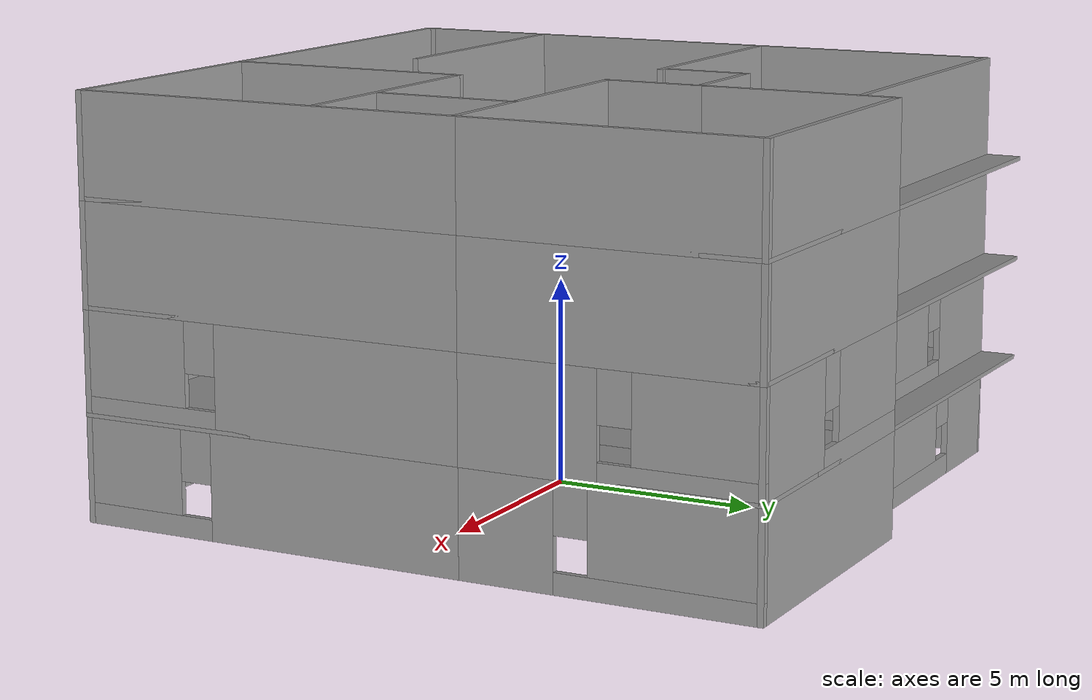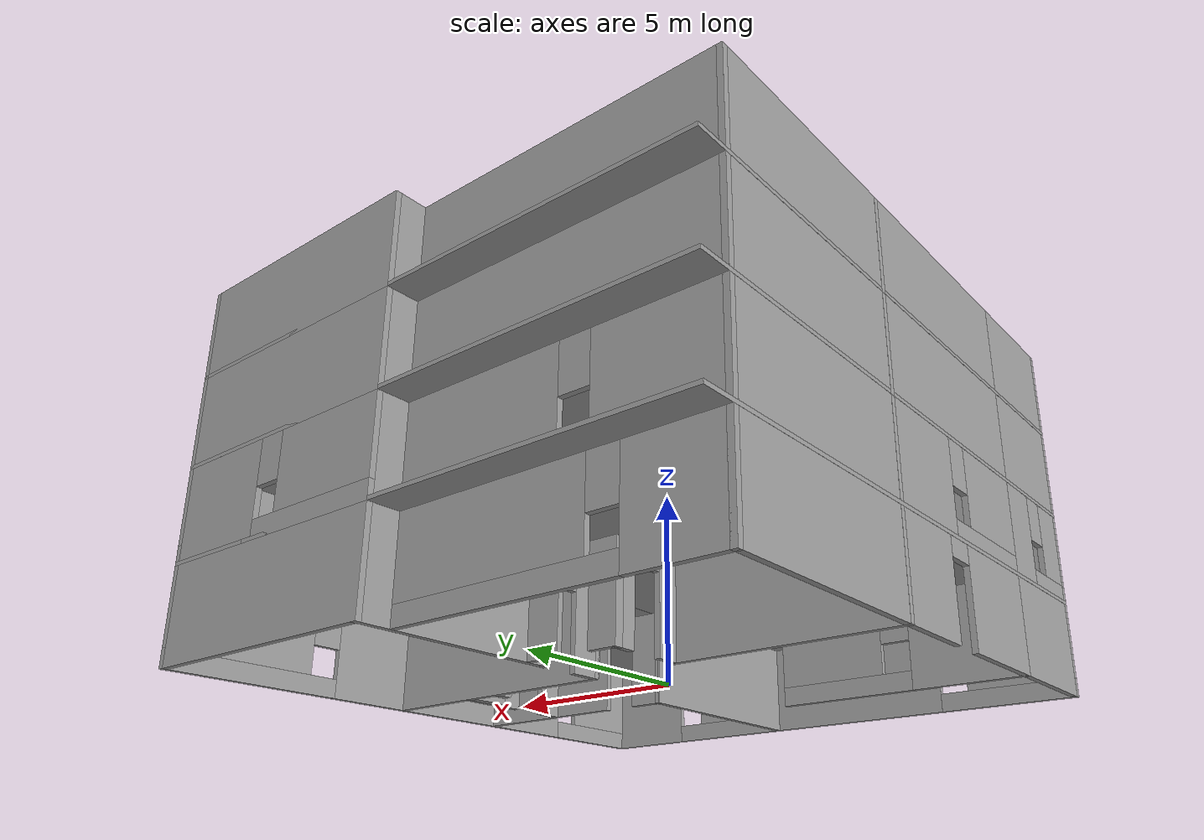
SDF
<?xml version='1.0'?>
<sdf version='1.7'>
  <model name='Drone_House'>
    <pose>0.336432 0.443828 0 0 -0 0</pose>
    <link name='Floor_0'>
      <pose>-1e-06 0 2.5 0 -0 0</pose>
      <visual name='Floor_0_Visual_0'>
        <pose>-3.13292 0 0.05 0 -0 0</pose>
        <geometry>
          <box>
            <size>9.33629 16.85 0.1</size>
          </box>
        </geometry>
        <material>
          <script>
            <uri>file://media/materials/scripts/gazebo.material</uri>
            <name>Gazebo/Grey</name>
          </script>
          <ambient>1 1 1 1</ambient>
        </material>
        <meta>
          <layer>1</layer>
        </meta>
      </visual>
      <collision name='Floor_0_Collision_0'>
        <geometry>
          <box>
            <size>9.33629 16.85 0.1</size>
          </box>
        </geometry>
        <pose>-3.13292 0 0.05 0 -0 0</pose>
      </collision>
      <visual name='Floor_0_Visual_1'>
        <pose>4.66814 -4.13229 0.05 0 -0 0</pose>
        <geometry>
          <box>
            <size>6.26584 8.58542 0.1</size>
          </box>
        </geometry>
        <material>
          <script>
            <uri>file://media/materials/scripts/gazebo.material</uri>
            <name>Gazebo/Grey</name>
          </script>
          <ambient>1 1 1 1</ambient>
        </material>
        <meta>
          <layer>1</layer>
        </meta>
      </visual>
      <collision name='Floor_0_Collision_1'>
        <geometry>
          <box>
            <size>6.26584 8.58542 0.1</size>
          </box>
        </geometry>
        <pose>4.66814 -4.13229 0.05 0 -0 0</pose>
      </collision>
      <visual name='Floor_0_Visual_2'>
        <pose>6.41814 4.29271 0.05 0 -0 0</pose>
        <geometry>
          <box>
            <size>2.76584 8.26458 0.1</size>
          </box>
        </geometry>
        <material>
          <script>
            <uri>file://media/materials/scripts/gazebo.material</uri>
            <name>Gazebo/Grey</name>
          </script>
          <ambient>1 1 1 1</ambient>
        </material>
        <meta>
          <layer>1</layer>
        </meta>
      </visual>
      <collision name='Floor_0_Collision_2'>
        <geometry>
          <box>
            <size>2.76584 8.26458 0.1</size>
          </box>
        </geometry>
        <pose>6.41814 4.29271 0.05 0 -0 0</pose>
      </collision>
      <visual name='Floor_0_Visual_3'>
        <pose>3.28522 4.79271 0.05 0 -0 0</pose>
        <geometry>
          <box>
            <size>3.5 7.26458 0.1</size>
          </box>
        </geometry>
        <material>
          <script>
            <uri>file://media/materials/scripts/gazebo.material</uri>
            <name>Gazebo/Grey</name>
          </script>
          <ambient>1 1 1 1</ambient>
        </material>
        <meta>
          <layer>1</layer>
        </meta>
      </visual>
      <collision name='Floor_0_Collision_3'>
        <geometry>
          <box>
            <size>3.5 7.26458 0.1</size>
          </box>
        </geometry>
        <pose>3.28522 4.79271 0.05 0 -0 0</pose>
      </collision>
    </link>
    <link name='Floor_5'>
      <collision name='Floor_5_Collision'>
        <geometry>
          <box>
            <size>15.6021 16.85 0.1</size>
          </box>
        </geometry>
        <pose>0 0 0.05 0 -0 0</pose>
      </collision>
      <visual name='Floor_5_Visual'>
        <pose>0 0 0.05 0 -0 0</pose>
        <geometry>
          <box>
            <size>15.6021 16.85 0.1</size>
          </box>
        </geometry>
        <material>
          <script>
            <uri>file://media/materials/scripts/gazebo.material</uri>
            <name>Gazebo/Grey</name>
          </script>
          <ambient>1 1 1 1</ambient>
        </material>
        <meta>
          <layer>2</layer>
        </meta>
      </visual>
      <pose>-1e-06 0 5 0 -0 0</pose>
    </link>
    <link name='Floor_6'>
      <collision name='Floor_6_Collision'>
        <geometry>
          <box>
            <size>15.6021 16.85 0.1</size>
          </box>
        </geometry>
        <pose>0 0 0.05 0 -0 0</pose>
      </collision>
      <visual name='Floor_6_Visual'>
        <pose>0 0 0.05 0 -0 0</pose>
        <geometry>
          <box>
            <size>15.6021 16.85 0.1</size>
          </box>
        </geometry>
        <material>
          <script>
            <uri>file://media/materials/scripts/gazebo.material</uri>
            <name>Gazebo/Grey</name>
          </script>
          <ambient>1 1 1 1</ambient>
        </material>
        <meta>
          <layer>3</layer>
        </meta>
      </visual>
      <pose>-1e-06 0 7.5 0 -0 0</pose>
    </link>
    <link name='Stairs_0'>
      <visual name='Stairs_0_Visual_0'>
        <pose>4.91856 0.660416 0.083333 0 -0 -1.5708</pose>
        <geometry>
          <box>
            <size>1 0.233333 0.166667</size>
          </box>
        </geometry>
        <material>
          <script>
            <uri>file://media/materials/scripts/gazebo.material</uri>
            <name>Gazebo/Grey</name>
          </script>
          <ambient>1 1 1 1</ambient>
        </material>
        <meta>
          <layer>0</layer>
        </meta>
      </visual>
      <collision name='Stairs_0_Collision_0'>
        <geometry>
          <box>
            <size>1 0.233333 0.166667</size>
          </box>
        </geometry>
        <pose>4.91856 0.660416 0.083333 0 -0 -1.5708</pose>
      </collision>
      <visual name='Stairs_0_Visual_1'>
        <pose>4.68522 0.660416 0.25 0 -0 -1.5708</pose>
        <geometry>
          <box>
            <size>1 0.233333 0.166667</size>
          </box>
        </geometry>
        <material>
          <script>
            <uri>file://media/materials/scripts/gazebo.material</uri>
            <name>Gazebo/Grey</name>
          </script>
          <ambient>1 1 1 1</ambient>
        </material>
        <meta>
          <layer>0</layer>
        </meta>
      </visual>
      <collision name='Stairs_0_Collision_1'>
        <geometry>
          <box>
            <size>1 0.233333 0.166667</size>
          </box>
        </geometry>
        <pose>4.68522 0.660416 0.25 0 -0 -1.5708</pose>
      </collision>
      <visual name='Stairs_0_Visual_2'>
        <pose>4.45189 0.660416 0.416667 0 -0 -1.5708</pose>
        <geometry>
          <box>
            <size>1 0.233333 0.166667</size>
          </box>
        </geometry>
        <material>
          <script>
            <uri>file://media/materials/scripts/gazebo.material</uri>
            <name>Gazebo/Grey</name>
          </script>
          <ambient>1 1 1 1</ambient>
        </material>
        <meta>
          <layer>0</layer>
        </meta>
      </visual>
      <collision name='Stairs_0_Collision_2'>
        <geometry>
          <box>
            <size>1 0.233333 0.166667</size>
          </box>
        </geometry>
        <pose>4.45189 0.660416 0.416667 0 -0 -1.5708</pose>
      </collision>
      <visual name='Stairs_0_Visual_3'>
        <pose>4.21856 0.660416 0.583333 0 -0 -1.5708</pose>
        <geometry>
          <box>
            <size>1 0.233333 0.166667</size>
          </box>
        </geometry>
        <material>
          <script>
            <uri>file://media/materials/scripts/gazebo.material</uri>
            <name>Gazebo/Grey</name>
          </script>
          <ambient>1 1 1 1</ambient>
        </material>
        <meta>
          <layer>0</layer>
        </meta>
      </visual>
      <collision name='Stairs_0_Collision_3'>
        <geometry>
          <box>
            <size>1 0.233333 0.166667</size>
          </box>
        </geometry>
        <pose>4.21856 0.660416 0.583333 0 -0 -1.5708</pose>
      </collision>
      <visual name='Stairs_0_Visual_4'>
        <pose>3.98522 0.660417 0.75 0 -0 -1.5708</pose>
        <geometry>
          <box>
            <size>1 0.233333 0.166667</size>
          </box>
        </geometry>
        <material>
          <script>
            <uri>file://media/materials/scripts/gazebo.material</uri>
            <name>Gazebo/Grey</name>
          </script>
          <ambient>1 1 1 1</ambient>
        </material>
        <meta>
          <layer>0</layer>
        </meta>
      </visual>
      <collision name='Stairs_0_Collision_4'>
        <geometry>
          <box>
            <size>1 0.233333 0.166667</size>
          </box>
        </geometry>
        <pose>3.98522 0.660417 0.75 0 -0 -1.5708</pose>
      </collision>
      <visual name='Stairs_0_Visual_5'>
        <pose>3.75189 0.660417 0.916667 0 -0 -1.5708</pose>
        <geometry>
          <box>
            <size>1 0.233333 0.166667</size>
          </box>
        </geometry>
        <material>
          <script>
            <uri>file://media/materials/scripts/gazebo.material</uri>
            <name>Gazebo/Grey</name>
          </script>
          <ambient>1 1 1 1</ambient>
        </material>
        <meta>
          <layer>0</layer>
        </meta>
      </visual>
      <collision name='Stairs_0_Collision_5'>
        <geometry>
          <box>
            <size>1 0.233333 0.166667</size>
          </box>
        </geometry>
        <pose>3.75189 0.660417 0.916667 0 -0 -1.5708</pose>
      </collision>
      <visual name='Stairs_0_Visual_6'>
        <pose>3.51856 0.660417 1.08333 0 -0 -1.5708</pose>
        <geometry>
          <box>
            <size>1 0.233333 0.166667</size>
          </box>
        </geometry>
        <material>
          <script>
            <uri>file://media/materials/scripts/gazebo.material</uri>
            <name>Gazebo/Grey</name>
          </script>
          <ambient>1 1 1 1</ambient>
        </material>
        <meta>
          <layer>0</layer>
        </meta>
      </visual>
      <collision name='Stairs_0_Collision_6'>
        <geometry>
          <box>
            <size>1 0.233333 0.166667</size>
          </box>
        </geometry>
        <pose>3.51856 0.660417 1.08333 0 -0 -1.5708</pose>
      </collision>
      <visual name='Stairs_0_Visual_7'>
        <pose>3.28522 0.660417 1.25 0 -0 -1.5708</pose>
        <geometry>
          <box>
            <size>1 0.233333 0.166667</size>
          </box>
        </geometry>
        <material>
          <script>
            <uri>file://media/materials/scripts/gazebo.material</uri>
            <name>Gazebo/Grey</name>
          </script>
          <ambient>1 1 1 1</ambient>
        </material>
        <meta>
          <layer>0</layer>
        </meta>
      </visual>
      <collision name='Stairs_0_Collision_7'>
        <geometry>
          <box>
            <size>1 0.233333 0.166667</size>
          </box>
        </geometry>
        <pose>3.28522 0.660417 1.25 0 -0 -1.5708</pose>
      </collision>
      <visual name='Stairs_0_Visual_8'>
        <pose>3.05189 0.660417 1.41667 0 -0 -1.5708</pose>
        <geometry>
          <box>
            <size>1 0.233333 0.166667</size>
          </box>
        </geometry>
        <material>
          <script>
            <uri>file://media/materials/scripts/gazebo.material</uri>
            <name>Gazebo/Grey</name>
          </script>
          <ambient>1 1 1 1</ambient>
        </material>
        <meta>
          <layer>0</layer>
        </meta>
      </visual>
      <collision name='Stairs_0_Collision_8'>
        <geometry>
          <box>
            <size>1 0.233333 0.166667</size>
          </box>
        </geometry>
        <pose>3.05189 0.660417 1.41667 0 -0 -1.5708</pose>
      </collision>
      <visual name='Stairs_0_Visual_9'>
        <pose>2.81856 0.660417 1.58333 0 -0 -1.5708</pose>
        <geometry>
          <box>
            <size>1 0.233333 0.166667</size>
          </box>
        </geometry>
        <material>
          <script>
            <uri>file://media/materials/scripts/gazebo.material</uri>
            <name>Gazebo/Grey</name>
          </script>
          <ambient>1 1 1 1</ambient>
        </material>
        <meta>
          <layer>0</layer>
        </meta>
      </visual>
      <collision name='Stairs_0_Collision_9'>
        <geometry>
          <box>
            <size>1 0.233333 0.166667</size>
          </box>
        </geometry>
        <pose>2.81856 0.660417 1.58333 0 -0 -1.5708</pose>
      </collision>
      <visual name='Stairs_0_Visual_10'>
        <pose>2.58522 0.660417 1.75 0 -0 -1.5708</pose>
        <geometry>
          <box>
            <size>1 0.233333 0.166667</size>
          </box>
        </geometry>
        <material>
          <script>
            <uri>file://media/materials/scripts/gazebo.material</uri>
            <name>Gazebo/Grey</name>
          </script>
          <ambient>1 1 1 1</ambient>
        </material>
        <meta>
          <layer>0</layer>
        </meta>
      </visual>
      <collision name='Stairs_0_Collision_10'>
        <geometry>
          <box>
            <size>1 0.233333 0.166667</size>
          </box>
        </geometry>
        <pose>2.58522 0.660417 1.75 0 -0 -1.5708</pose>
      </collision>
      <visual name='Stairs_0_Visual_11'>
        <pose>2.35189 0.660417 1.91667 0 -0 -1.5708</pose>
        <geometry>
          <box>
            <size>1 0.233333 0.166667</size>
          </box>
        </geometry>
        <material>
          <script>
            <uri>file://media/materials/scripts/gazebo.material</uri>
            <name>Gazebo/Grey</name>
          </script>
          <ambient>1 1 1 1</ambient>
        </material>
        <meta>
          <layer>0</layer>
        </meta>
      </visual>
      <collision name='Stairs_0_Collision_11'>
        <geometry>
          <box>
            <size>1 0.233333 0.166667</size>
          </box>
        </geometry>
        <pose>2.35189 0.660417 1.91667 0 -0 -1.5708</pose>
      </collision>
      <visual name='Stairs_0_Visual_12'>
        <pose>2.11856 0.660417 2.08333 0 -0 -1.5708</pose>
        <geometry>
          <box>
            <size>1 0.233333 0.166667</size>
          </box>
        </geometry>
        <material>
          <script>
            <uri>file://media/materials/scripts/gazebo.material</uri>
            <name>Gazebo/Grey</name>
          </script>
          <ambient>1 1 1 1</ambient>
        </material>
        <meta>
          <layer>0</layer>
        </meta>
      </visual>
      <collision name='Stairs_0_Collision_12'>
        <geometry>
          <box>
            <size>1 0.233333 0.166667</size>
          </box>
        </geometry>
        <pose>2.11856 0.660417 2.08333 0 -0 -1.5708</pose>
      </collision>
      <visual name='Stairs_0_Visual_13'>
        <pose>1.88522 0.660417 2.25 0 -0 -1.5708</pose>
        <geometry>
          <box>
            <size>1 0.233333 0.166667</size>
          </box>
        </geometry>
        <material>
          <script>
            <uri>file://media/materials/scripts/gazebo.material</uri>
            <name>Gazebo/Grey</name>
          </script>
          <ambient>1 1 1 1</ambient>
        </material>
        <meta>
          <layer>0</layer>
        </meta>
      </visual>
      <collision name='Stairs_0_Collision_13'>
        <geometry>
          <box>
            <size>1 0.233333 0.166667</size>
          </box>
        </geometry>
        <pose>1.88522 0.660417 2.25 0 -0 -1.5708</pose>
      </collision>
      <visual name='Stairs_0_Visual_14'>
        <pose>1.65189 0.660417 2.41667 0 -0 -1.5708</pose>
        <geometry>
          <box>
            <size>1 0.233333 0.166667</size>
          </box>
        </geometry>
        <material>
          <script>
            <uri>file://media/materials/scripts/gazebo.material</uri>
            <name>Gazebo/Grey</name>
          </script>
          <ambient>1 1 1 1</ambient>
        </material>
        <meta>
          <layer>0</layer>
        </meta>
      </visual>
      <collision name='Stairs_0_Collision_14'>
        <geometry>
          <box>
            <size>1 0.233333 0.166667</size>
          </box>
        </geometry>
        <pose>1.65189 0.660417 2.41667 0 -0 -1.5708</pose>
      </collision>
    </link>
    <link name='Wall_10'>
      <collision name='Wall_10_Collision'>
        <geometry>
          <box>
            <size>1 0.15 2.5</size>
          </box>
        </geometry>
        <pose>0 0 1.25 0 -0 0</pose>
      </collision>
      <visual name='Wall_10_Visual'>
        <pose>0 0 1.25 0 -0 0</pose>
        <geometry>
          <box>
            <size>1 0.15 2.5</size>
          </box>
        </geometry>
        <material>
          <script>
            <uri>file://media/materials/scripts/gazebo.material</uri>
            <name>Gazebo/Grey</name>
          </script>
          <ambient>1 1 1 1</ambient>
        </material>
        <meta>
          <layer>0</layer>
        </meta>
      </visual>
      <pose>0.626064 7.925 0 0 -0 1.5708</pose>
    </link>
    <link name='Wall_100'>
      <collision name='Wall_100_Collision'>
        <geometry>
          <box>
            <size>6.25 0.15 2.5</size>
          </box>
        </geometry>
        <pose>0 0 1.25 0 -0 0</pose>
      </collision>
      <visual name='Wall_100_Visual'>
        <pose>0 0 1.25 0 -0 0</pose>
        <geometry>
          <box>
            <size>6.25 0.15 2.5</size>
          </box>
        </geometry>
        <material>
          <script>
            <uri>file://media/materials/scripts/gazebo.material</uri>
            <name>Gazebo/Grey</name>
          </script>
          <ambient>1 1 1 1</ambient>
        </material>
        <meta>
          <layer>2</layer>
        </meta>
      </visual>
      <pose>1.37606 -5.3 5 0 -0 1.5708</pose>
    </link>
    <link name='Wall_101'>
      <collision name='Wall_101_Collision'>
        <geometry>
          <box>
            <size>6.5 0.15 2.5</size>
          </box>
        </geometry>
        <pose>0 0 1.25 0 -0 0</pose>
      </collision>
      <visual name='Wall_101_Visual'>
        <pose>0 0 1.25 0 -0 0</pose>
        <geometry>
          <box>
            <size>6.5 0.15 2.5</size>
          </box>
        </geometry>
        <material>
          <script>
            <uri>file://media/materials/scripts/gazebo.material</uri>
            <name>Gazebo/Grey</name>
          </script>
          <ambient>1 1 1 1</ambient>
        </material>
        <meta>
          <layer>2</layer>
        </meta>
      </visual>
      <pose>4.55106 -2.25 5 0 -0 0</pose>
    </link>
    <link name='Wall_102'>
      <collision name='Wall_102_Collision'>
        <geometry>
          <box>
            <size>3.5 0.15 2.5</size>
          </box>
        </geometry>
        <pose>0 0 1.25 0 -0 0</pose>
      </collision>
      <visual name='Wall_102_Visual'>
        <pose>0 0 1.25 0 -0 0</pose>
        <geometry>
          <box>
            <size>3.5 0.15 2.5</size>
          </box>
        </geometry>
        <material>
          <script>
            <uri>file://media/materials/scripts/gazebo.material</uri>
            <name>Gazebo/Grey</name>
          </script>
          <ambient>1 1 1 1</ambient>
        </material>
        <meta>
          <layer>2</layer>
        </meta>
      </visual>
      <pose>-7.72394 -6.525 5 0 -0 -1.5708</pose>
    </link>
    <link name='Wall_103'>
      <collision name='Wall_103_Collision'>
        <geometry>
          <box>
            <size>0.15 0.15 2.5</size>
          </box>
        </geometry>
        <pose>0 0 1.25 0 -0 0</pose>
      </collision>
      <visual name='Wall_103_Visual'>
        <pose>0 0 1.25 0 -0 0</pose>
        <geometry>
          <box>
            <size>0.15 0.15 2.5</size>
          </box>
        </geometry>
        <material>
          <script>
            <uri>file://media/materials/scripts/gazebo.material</uri>
            <name>Gazebo/Grey</name>
          </script>
          <ambient>1 1 1 1</ambient>
        </material>
        <meta>
          <layer>2</layer>
        </meta>
      </visual>
      <pose>-7.72394 -8.2 5 0 -0 0</pose>
    </link>
    <link name='Wall_104'>
      <collision name='Wall_104_Collision'>
        <geometry>
          <box>
            <size>9.25 0.15 2.5</size>
          </box>
        </geometry>
        <pose>0 0 1.25 0 -0 0</pose>
      </collision>
      <visual name='Wall_104_Visual'>
        <pose>0 0 1.25 0 -0 0</pose>
        <geometry>
          <box>
            <size>9.25 0.15 2.5</size>
          </box>
        </geometry>
        <material>
          <script>
            <uri>file://media/materials/scripts/gazebo.material</uri>
            <name>Gazebo/Grey</name>
          </script>
          <ambient>1 1 1 1</ambient>
        </material>
        <meta>
          <layer>2</layer>
        </meta>
      </visual>
      <pose>-3.17394 -8.35 5 0 -0 3.14159</pose>
    </link>
    <link name='Wall_105'>
      <collision name='Wall_105_Collision'>
        <geometry>
          <box>
            <size>3.5 0.15 2.5</size>
          </box>
        </geometry>
        <pose>0 0 1.25 0 -0 0</pose>
      </collision>
      <visual name='Wall_105_Visual'>
        <pose>0 0 1.25 0 -0 0</pose>
        <geometry>
          <box>
            <size>3.5 0.15 2.5</size>
          </box>
        </geometry>
        <material>
          <script>
            <uri>file://media/materials/scripts/gazebo.material</uri>
            <name>Gazebo/Grey</name>
          </script>
          <ambient>1 1 1 1</ambient>
        </material>
        <meta>
          <layer>2</layer>
        </meta>
      </visual>
      <pose>5.09404 -0.429379 5 0 -0 -1.5708</pose>
    </link>
    <link name='Wall_106'>
      <collision name='Wall_106_Collision'>
        <geometry>
          <box>
            <size>12.5 0.15 2.5</size>
          </box>
        </geometry>
        <pose>0 0 1.25 0 -0 0</pose>
      </collision>
      <visual name='Wall_106_Visual'>
        <pose>0 0 1.25 0 -0 0</pose>
        <geometry>
          <box>
            <size>12.5 0.15 2.5</size>
          </box>
        </geometry>
        <material>
          <script>
            <uri>file://media/materials/scripts/gazebo.material</uri>
            <name>Gazebo/Grey</name>
          </script>
          <ambient>1 1 1 1</ambient>
        </material>
        <meta>
          <layer>3</layer>
        </meta>
      </visual>
      <pose>-7.72394 1.325 7.5 0 -0 -1.5708</pose>
    </link>
    <link name='Wall_107'>
      <collision name='Wall_107_Collision'>
        <geometry>
          <box>
            <size>6.75 0.15 2.5</size>
          </box>
        </geometry>
        <pose>0 0 1.25 0 -0 0</pose>
      </collision>
      <visual name='Wall_107_Visual'>
        <pose>0 0 1.25 0 -0 0</pose>
        <geometry>
          <box>
            <size>6.75 0.15 2.5</size>
          </box>
        </geometry>
        <material>
          <script>
            <uri>file://media/materials/scripts/gazebo.material</uri>
            <name>Gazebo/Grey</name>
          </script>
          <ambient>1 1 1 1</ambient>
        </material>
        <meta>
          <layer>3</layer>
        </meta>
      </visual>
      <pose>-4.42394 -4.85 7.5 0 -0 0</pose>
    </link>
    <link name='Wall_108'>
      <collision name='Wall_108_Collision'>
        <geometry>
          <box>
            <size>6 0.15 2.5</size>
          </box>
        </geometry>
        <pose>0 0 1.25 0 -0 0</pose>
      </collision>
      <visual name='Wall_108_Visual'>
        <pose>0 0 1.25 0 -0 0</pose>
        <geometry>
          <box>
            <size>6 0.15 2.5</size>
          </box>
        </geometry>
        <material>
          <script>
            <uri>file://media/materials/scripts/gazebo.material</uri>
            <name>Gazebo/Grey</name>
          </script>
          <ambient>1 1 1 1</ambient>
        </material>
        <meta>
          <layer>3</layer>
        </meta>
      </visual>
      <pose>-4.80107 1.443 7.5 0 -0 0</pose>
    </link>
    <link name='Wall_109'>
      <collision name='Wall_109_Collision'>
        <geometry>
          <box>
            <size>8.5 0.15 2.5</size>
          </box>
        </geometry>
        <pose>0 0 1.25 0 -0 0</pose>
      </collision>
      <visual name='Wall_109_Visual'>
        <pose>0 0 1.25 0 -0 0</pose>
        <geometry>
          <box>
            <size>8.5 0.15 2.5</size>
          </box>
        </geometry>
        <material>
          <script>
            <uri>file://media/materials/scripts/gazebo.material</uri>
            <name>Gazebo/Grey</name>
          </script>
          <ambient>1 1 1 1</ambient>
        </material>
        <meta>
          <layer>3</layer>
        </meta>
      </visual>
      <pose>-3.54894 7.5 7.5 0 -0 0</pose>
    </link>
    <link name='Wall_11'>
      <collision name='Wall_11_Collision'>
        <geometry>
          <box>
            <size>5.25 0.15 2.5</size>
          </box>
        </geometry>
        <pose>0 0 1.25 0 -0 0</pose>
      </collision>
      <visual name='Wall_11_Visual'>
        <pose>0 0 1.25 0 -0 0</pose>
        <geometry>
          <box>
            <size>5.25 0.15 2.5</size>
          </box>
        </geometry>
        <material>
          <script>
            <uri>file://media/materials/scripts/gazebo.material</uri>
            <name>Gazebo/Grey</name>
          </script>
          <ambient>1 1 1 1</ambient>
        </material>
        <meta>
          <layer>0</layer>
        </meta>
      </visual>
      <pose>0.626064 5.8 0 0 -0 -1.5708</pose>
    </link>
    <link name='Wall_110'>
      <collision name='Wall_110_Collision'>
        <geometry>
          <box>
            <size>1 0.15 2.5</size>
          </box>
        </geometry>
        <pose>0 0 1.25 0 -0 0</pose>
      </collision>
      <visual name='Wall_110_Visual'>
        <pose>0 0 1.25 0 -0 0</pose>
        <geometry>
          <box>
            <size>1 0.15 2.5</size>
          </box>
        </geometry>
        <material>
          <script>
            <uri>file://media/materials/scripts/gazebo.material</uri>
            <name>Gazebo/Grey</name>
          </script>
          <ambient>1 1 1 1</ambient>
        </material>
        <meta>
          <layer>3</layer>
        </meta>
      </visual>
      <pose>0.626064 7.925 7.5 0 -0 1.5708</pose>
    </link>
    <link name='Wall_111'>
      <collision name='Wall_111_Collision'>
        <geometry>
          <box>
            <size>5.25 0.15 2.5</size>
          </box>
        </geometry>
        <pose>0 0 1.25 0 -0 0</pose>
      </collision>
      <visual name='Wall_111_Visual'>
        <pose>0 0 1.25 0 -0 0</pose>
        <geometry>
          <box>
            <size>5.25 0.15 2.5</size>
          </box>
        </geometry>
        <material>
          <script>
            <uri>file://media/materials/scripts/gazebo.material</uri>
            <name>Gazebo/Grey</name>
          </script>
          <ambient>1 1 1 1</ambient>
        </material>
        <meta>
          <layer>3</layer>
        </meta>
      </visual>
      <pose>0.626064 5.8 7.5 0 -0 -1.5708</pose>
    </link>
    <link name='Wall_112'>
      <collision name='Wall_112_Collision'>
        <geometry>
          <box>
            <size>0.5 0.15 2.5</size>
          </box>
        </geometry>
        <pose>0 0 1.25 0 -0 0</pose>
      </collision>
      <visual name='Wall_112_Visual'>
        <pose>0 0 1.25 0 -0 0</pose>
        <geometry>
          <box>
            <size>0.5 0.15 2.5</size>
          </box>
        </geometry>
        <material>
          <script>
            <uri>file://media/materials/scripts/gazebo.material</uri>
            <name>Gazebo/Grey</name>
          </script>
          <ambient>1 1 1 1</ambient>
        </material>
        <meta>
          <layer>3</layer>
        </meta>
      </visual>
      <pose>0.626064 3.425 7.5 0 -0 1.5708</pose>
    </link>
    <link name='Wall_113'>
      <collision name='Wall_113_Collision'>
        <geometry>
          <box>
            <size>2.75 0.15 2.5</size>
          </box>
        </geometry>
        <pose>0 0 1.25 0 -0 0</pose>
      </collision>
      <visual name='Wall_113_Visual'>
        <pose>0 0 1.25 0 -0 0</pose>
        <geometry>
          <box>
            <size>2.75 0.15 2.5</size>
          </box>
        </geometry>
        <material>
          <script>
            <uri>file://media/materials/scripts/gazebo.material</uri>
            <name>Gazebo/Grey</name>
          </script>
          <ambient>1 1 1 1</ambient>
        </material>
        <meta>
          <layer>3</layer>
        </meta>
      </visual>
      <pose>-0.673936 3.6 7.5 0 -0 3.14159</pose>
    </link>
    <link name='Wall_114'>
      <collision name='Wall_114_Collision'>
        <geometry>
          <box>
            <size>0.25 0.15 2.5</size>
          </box>
        </geometry>
        <pose>0 0 1.25 0 -0 0</pose>
      </collision>
      <visual name='Wall_114_Visual'>
        <pose>0 0 1.25 0 -0 0</pose>
        <geometry>
          <box>
            <size>0.25 0.15 2.5</size>
          </box>
        </geometry>
        <material>
          <script>
            <uri>file://media/materials/scripts/gazebo.material</uri>
            <name>Gazebo/Grey</name>
          </script>
          <ambient>1 1 1 1</ambient>
        </material>
        <meta>
          <layer>3</layer>
        </meta>
      </visual>
      <pose>-1.97394 3.55 7.5 0 -0 -1.5708</pose>
    </link>
    <link name='Wall_115'>
      <collision name='Wall_115_Collision'>
        <geometry>
          <box>
            <size>2.25 0.15 2.5</size>
          </box>
        </geometry>
        <pose>0 0 1.25 0 -0 0</pose>
      </collision>
      <visual name='Wall_115_Visual'>
        <pose>0 0 1.25 0 -0 0</pose>
        <geometry>
          <box>
            <size>2.25 0.15 2.5</size>
          </box>
        </geometry>
        <material>
          <script>
            <uri>file://media/materials/scripts/gazebo.material</uri>
            <name>Gazebo/Grey</name>
          </script>
          <ambient>1 1 1 1</ambient>
        </material>
        <meta>
          <layer>3</layer>
        </meta>
      </visual>
      <pose>-1.97394 2.55 7.5 0 -0 -1.5708</pose>
    </link>
    <link name='Wall_116'>
      <collision name='Wall_116_Collision'>
        <geometry>
          <box>
            <size>2.5 0.15 2.5</size>
          </box>
        </geometry>
        <pose>0 0 1.25 0 -0 0</pose>
      </collision>
      <visual name='Wall_116_Visual'>
        <pose>0 0 1.25 0 -0 0</pose>
        <geometry>
          <box>
            <size>2.5 0.15 2.5</size>
          </box>
        </geometry>
        <material>
          <script>
            <uri>file://media/materials/scripts/gazebo.material</uri>
            <name>Gazebo/Grey</name>
          </script>
          <ambient>1 1 1 1</ambient>
        </material>
        <meta>
          <layer>3</layer>
        </meta>
      </visual>
      <pose>0.626064 2.425 7.5 0 -0 -1.5708</pose>
    </link>
    <link name='Wall_117'>
      <collision name='Wall_117_Collision'>
        <geometry>
          <box>
            <size>7.25 0.15 2.5</size>
          </box>
        </geometry>
        <pose>0 0 1.25 0 -0 0</pose>
      </collision>
      <visual name='Wall_117_Visual'>
        <pose>0 0 1.25 0 -0 0</pose>
        <geometry>
          <box>
            <size>7.25 0.15 2.5</size>
          </box>
        </geometry>
        <material>
          <script>
            <uri>file://media/materials/scripts/gazebo.material</uri>
            <name>Gazebo/Grey</name>
          </script>
          <ambient>1 1 1 1</ambient>
        </material>
        <meta>
          <layer>3</layer>
        </meta>
      </visual>
      <pose>4.17606 1.25 7.5 0 -0 0</pose>
    </link>
    <link name='Wall_118'>
      <collision name='Wall_118_Collision'>
        <geometry>
          <box>
            <size>7.25 0.15 2.5</size>
          </box>
        </geometry>
        <pose>0 0 1.25 0 -0 0</pose>
      </collision>
      <visual name='Wall_118_Visual'>
        <pose>0 0 1.25 0 -0 0</pose>
        <geometry>
          <box>
            <size>7.25 0.15 2.5</size>
          </box>
        </geometry>
        <material>
          <script>
            <uri>file://media/materials/scripts/gazebo.material</uri>
            <name>Gazebo/Grey</name>
          </script>
          <ambient>1 1 1 1</ambient>
        </material>
        <meta>
          <layer>3</layer>
        </meta>
      </visual>
      <pose>7.72606 4.8 7.5 0 -0 1.5708</pose>
    </link>
    <link name='Wall_119'>
      <collision name='Wall_119_Collision'>
        <geometry>
          <box>
            <size>7.25 0.15 2.5</size>
          </box>
        </geometry>
        <pose>0 0 1.25 0 -0 0</pose>
      </collision>
      <visual name='Wall_119_Visual'>
        <pose>0 0 1.25 0 -0 0</pose>
        <geometry>
          <box>
            <size>7.25 0.15 2.5</size>
          </box>
        </geometry>
        <material>
          <script>
            <uri>file://media/materials/scripts/gazebo.material</uri>
            <name>Gazebo/Grey</name>
          </script>
          <ambient>1 1 1 1</ambient>
        </material>
        <meta>
          <layer>3</layer>
        </meta>
      </visual>
      <pose>4.17606 8.35 7.5 0 -0 3.14159</pose>
    </link>
    <link name='Wall_12'>
      <collision name='Wall_12_Collision'>
        <geometry>
          <box>
            <size>0.5 0.15 2.5</size>
          </box>
        </geometry>
        <pose>0 0 1.25 0 -0 0</pose>
      </collision>
      <visual name='Wall_12_Visual'>
        <pose>0 0 1.25 0 -0 0</pose>
        <geometry>
          <box>
            <size>0.5 0.15 2.5</size>
          </box>
        </geometry>
        <material>
          <script>
            <uri>file://media/materials/scripts/gazebo.material</uri>
            <name>Gazebo/Grey</name>
          </script>
          <ambient>1 1 1 1</ambient>
        </material>
        <meta>
          <layer>0</layer>
        </meta>
      </visual>
      <pose>0.626064 3.425 0 0 -0 1.5708</pose>
    </link>
    <link name='Wall_120'>
      <collision name='Wall_120_Collision'>
        <geometry>
          <box>
            <size>9.75 0.15 2.5</size>
          </box>
        </geometry>
        <pose>0 0 1.25 0 -0 0</pose>
      </collision>
      <visual name='Wall_120_Visual'>
        <pose>0 0 1.25 0 -0 0</pose>
        <geometry>
          <box>
            <size>9.75 0.15 2.5</size>
          </box>
        </geometry>
        <material>
          <script>
            <uri>file://media/materials/scripts/gazebo.material</uri>
            <name>Gazebo/Grey</name>
          </script>
          <ambient>1 1 1 1</ambient>
        </material>
        <meta>
          <layer>3</layer>
        </meta>
      </visual>
      <pose>7.72606 -3.55 7.5 0 -0 -1.5708</pose>
    </link>
    <link name='Wall_121'>
      <collision name='Wall_121_Collision'>
        <geometry>
          <box>
            <size>6.5 0.15 2.5</size>
          </box>
        </geometry>
        <pose>0 0 1.25 0 -0 0</pose>
      </collision>
      <visual name='Wall_121_Visual'>
        <pose>0 0 1.25 0 -0 0</pose>
        <geometry>
          <box>
            <size>6.5 0.15 2.5</size>
          </box>
        </geometry>
        <material>
          <script>
            <uri>file://media/materials/scripts/gazebo.material</uri>
            <name>Gazebo/Grey</name>
          </script>
          <ambient>1 1 1 1</ambient>
        </material>
        <meta>
          <layer>3</layer>
        </meta>
      </visual>
      <pose>4.55106 -8.35 7.5 0 -0 3.14159</pose>
    </link>
    <link name='Wall_122'>
      <collision name='Wall_122_Collision'>
        <geometry>
          <box>
            <size>6.25 0.15 2.5</size>
          </box>
        </geometry>
        <pose>0 0 1.25 0 -0 0</pose>
      </collision>
      <visual name='Wall_122_Visual'>
        <pose>0 0 1.25 0 -0 0</pose>
        <geometry>
          <box>
            <size>6.25 0.15 2.5</size>
          </box>
        </geometry>
        <material>
          <script>
            <uri>file://media/materials/scripts/gazebo.material</uri>
            <name>Gazebo/Grey</name>
          </script>
          <ambient>1 1 1 1</ambient>
        </material>
        <meta>
          <layer>3</layer>
        </meta>
      </visual>
      <pose>1.37606 -5.3 7.5 0 -0 1.5708</pose>
    </link>
    <link name='Wall_123'>
      <collision name='Wall_123_Collision'>
        <geometry>
          <box>
            <size>6.5 0.15 2.5</size>
          </box>
        </geometry>
        <pose>0 0 1.25 0 -0 0</pose>
      </collision>
      <visual name='Wall_123_Visual'>
        <pose>0 0 1.25 0 -0 0</pose>
        <geometry>
          <box>
            <size>6.5 0.15 2.5</size>
          </box>
        </geometry>
        <material>
          <script>
            <uri>file://media/materials/scripts/gazebo.material</uri>
            <name>Gazebo/Grey</name>
          </script>
          <ambient>1 1 1 1</ambient>
        </material>
        <meta>
          <layer>3</layer>
        </meta>
      </visual>
      <pose>4.55106 -2.25 7.5 0 -0 0</pose>
    </link>
    <link name='Wall_124'>
      <collision name='Wall_124_Collision'>
        <geometry>
          <box>
            <size>3.5 0.15 2.5</size>
          </box>
        </geometry>
        <pose>0 0 1.25 0 -0 0</pose>
      </collision>
      <visual name='Wall_124_Visual'>
        <pose>0 0 1.25 0 -0 0</pose>
        <geometry>
          <box>
            <size>3.5 0.15 2.5</size>
          </box>
        </geometry>
        <material>
          <script>
            <uri>file://media/materials/scripts/gazebo.material</uri>
            <name>Gazebo/Grey</name>
          </script>
          <ambient>1 1 1 1</ambient>
        </material>
        <meta>
          <layer>3</layer>
        </meta>
      </visual>
      <pose>-7.72394 -6.525 7.5 0 -0 -1.5708</pose>
    </link>
    <link name='Wall_125'>
      <collision name='Wall_125_Collision'>
        <geometry>
          <box>
            <size>0.15 0.15 2.5</size>
          </box>
        </geometry>
        <pose>0 0 1.25 0 -0 0</pose>
      </collision>
      <visual name='Wall_125_Visual'>
        <pose>0 0 1.25 0 -0 0</pose>
        <geometry>
          <box>
            <size>0.15 0.15 2.5</size>
          </box>
        </geometry>
        <material>
          <script>
            <uri>file://media/materials/scripts/gazebo.material</uri>
            <name>Gazebo/Grey</name>
          </script>
          <ambient>1 1 1 1</ambient>
        </material>
        <meta>
          <layer>3</layer>
        </meta>
      </visual>
      <pose>-7.72394 -8.2 7.5 0 -0 0</pose>
    </link>
    <link name='Wall_126'>
      <collision name='Wall_126_Collision'>
        <geometry>
          <box>
            <size>9.25 0.15 2.5</size>
          </box>
        </geometry>
        <pose>0 0 1.25 0 -0 0</pose>
      </collision>
      <visual name='Wall_126_Visual'>
        <pose>0 0 1.25 0 -0 0</pose>
        <geometry>
          <box>
            <size>9.25 0.15 2.5</size>
          </box>
        </geometry>
        <material>
          <script>
            <uri>file://media/materials/scripts/gazebo.material</uri>
            <name>Gazebo/Grey</name>
          </script>
          <ambient>1 1 1 1</ambient>
        </material>
        <meta>
          <layer>3</layer>
        </meta>
      </visual>
      <pose>-3.17394 -8.35 7.5 0 -0 3.14159</pose>
    </link>
    <link name='Wall_127'>
      <collision name='Wall_127_Collision'>
        <geometry>
          <box>
            <size>3.5 0.15 2.5</size>
          </box>
        </geometry>
        <pose>0 0 1.25 0 -0 0</pose>
      </collision>
      <visual name='Wall_127_Visual'>
        <pose>0 0 1.25 0 -0 0</pose>
        <geometry>
          <box>
            <size>3.5 0.15 2.5</size>
          </box>
        </geometry>
        <material>
          <script>
            <uri>file://media/materials/scripts/gazebo.material</uri>
            <name>Gazebo/Grey</name>
          </script>
          <ambient>1 1 1 1</ambient>
        </material>
        <meta>
          <layer>3</layer>
        </meta>
      </visual>
      <pose>5.09404 -0.429379 7.5 0 -0 -1.5708</pose>
    </link>
    <link name='Wall_13'>
      <pose>-0.673936 3.6 0 0 -0 3.14159</pose>
      <visual name='Wall_13_Visual_0'>
        <pose>-0.843864 0 1.25 0 -0 0</pose>
        <geometry>
          <box>
            <size>1.06227 0.15 2.5</size>
          </box>
        </geometry>
        <material>
          <script>
            <uri>file://media/materials/scripts/gazebo.material</uri>
            <name>Gazebo/Grey</name>
          </script>
          <ambient>1 1 1 1</ambient>
        </material>
        <meta>
          <layer>0</layer>
        </meta>
      </visual>
      <collision name='Wall_13_Collision_0'>
        <geometry>
          <box>
            <size>1.06227 0.15 2.5</size>
          </box>
        </geometry>
        <pose>-0.843864 0 1.25 0 -0 0</pose>
      </collision>
      <visual name='Wall_13_Visual_1'>
        <pose>0.981136 0 1.25 0 -0 0</pose>
        <geometry>
          <box>
            <size>0.787728 0.15 2.5</size>
          </box>
        </geometry>
        <material>
          <script>
            <uri>file://media/materials/scripts/gazebo.material</uri>
            <name>Gazebo/Grey</name>
          </script>
          <ambient>1 1 1 1</ambient>
        </material>
        <meta>
          <layer>0</layer>
        </meta>
      </visual>
      <collision name='Wall_13_Collision_1'>
        <geometry>
          <box>
            <size>0.787728 0.15 2.5</size>
          </box>
        </geometry>
        <pose>0.981136 0 1.25 0 -0 0</pose>
      </collision>
      <visual name='Wall_13_Visual_2'>
        <pose>0.137272 0 2.25 0 -0 0</pose>
        <geometry>
          <box>
            <size>0.9 0.15 0.5</size>
          </box>
        </geometry>
        <material>
          <script>
            <uri>file://media/materials/scripts/gazebo.material</uri>
            <name>Gazebo/Grey</name>
          </script>
          <ambient>1 1 1 1</ambient>
        </material>
        <meta>
          <layer>0</layer>
        </meta>
      </visual>
      <collision name='Wall_13_Collision_2'>
        <geometry>
          <box>
            <size>0.9 0.15 0.5</size>
          </box>
        </geometry>
        <pose>0.137272 0 2.25 0 -0 0</pose>
      </collision>
    </link>
    <link name='Wall_14'>
      <collision name='Wall_14_Collision'>
        <geometry>
          <box>
            <size>0.25 0.15 2.5</size>
          </box>
        </geometry>
        <pose>0 0 1.25 0 -0 0</pose>
      </collision>
      <visual name='Wall_14_Visual'>
        <pose>0 0 1.25 0 -0 0</pose>
        <geometry>
          <box>
            <size>0.25 0.15 2.5</size>
          </box>
        </geometry>
        <material>
          <script>
            <uri>file://media/materials/scripts/gazebo.material</uri>
            <name>Gazebo/Grey</name>
          </script>
          <ambient>1 1 1 1</ambient>
        </material>
        <meta>
          <layer>0</layer>
        </meta>
      </visual>
      <pose>-1.97394 3.55 0 0 -0 -1.5708</pose>
    </link>
    <link name='Wall_16'>
      <pose>-1.97394 2.55 0 0 -0 -1.5708</pose>
      <visual name='Wall_16_Visual_0'>
        <pose>-0.800315 0 1.25 0 -0 0</pose>
        <geometry>
          <box>
            <size>0.649369 0.15 2.5</size>
          </box>
        </geometry>
        <material>
          <script>
            <uri>file://media/materials/scripts/gazebo.material</uri>
            <name>Gazebo/Grey</name>
          </script>
          <ambient>1 1 1 1</ambient>
        </material>
        <meta>
          <layer>0</layer>
        </meta>
      </visual>
      <collision name='Wall_16_Collision_0'>
        <geometry>
          <box>
            <size>0.649369 0.15 2.5</size>
          </box>
        </geometry>
        <pose>-0.800315 0 1.25 0 -0 0</pose>
      </collision>
      <visual name='Wall_16_Visual_1'>
        <pose>0.774685 0 1.25 0 -0 0</pose>
        <geometry>
          <box>
            <size>0.700631 0.15 2.5</size>
          </box>
        </geometry>
        <material>
          <script>
            <uri>file://media/materials/scripts/gazebo.material</uri>
            <name>Gazebo/Grey</name>
          </script>
          <ambient>1 1 1 1</ambient>
        </material>
        <meta>
          <layer>0</layer>
        </meta>
      </visual>
      <collision name='Wall_16_Collision_1'>
        <geometry>
          <box>
            <size>0.700631 0.15 2.5</size>
          </box>
        </geometry>
        <pose>0.774685 0 1.25 0 -0 0</pose>
      </collision>
      <visual name='Wall_16_Visual_2'>
        <pose>-0.025631 0 2.25 0 -0 0</pose>
        <geometry>
          <box>
            <size>0.9 0.15 0.5</size>
          </box>
        </geometry>
        <material>
          <script>
            <uri>file://media/materials/scripts/gazebo.material</uri>
            <name>Gazebo/Grey</name>
          </script>
          <ambient>1 1 1 1</ambient>
        </material>
        <meta>
          <layer>0</layer>
        </meta>
      </visual>
      <collision name='Wall_16_Collision_2'>
        <geometry>
          <box>
            <size>0.9 0.15 0.5</size>
          </box>
        </geometry>
        <pose>-0.025631 0 2.25 0 -0 0</pose>
      </collision>
    </link>
    <link name='Wall_18'>
      <pose>0.626064 2.425 0 0 -0 -1.5708</pose>
      <visual name='Wall_18_Visual_0'>
        <pose>-0.898715 0 1.25 0 -0 0</pose>
        <geometry>
          <box>
            <size>0.70257 0.15 2.5</size>
          </box>
        </geometry>
        <material>
          <script>
            <uri>file://media/materials/scripts/gazebo.material</uri>
            <name>Gazebo/Grey</name>
          </script>
          <ambient>1 1 1 1</ambient>
        </material>
        <meta>
          <layer>0</layer>
        </meta>
      </visual>
      <collision name='Wall_18_Collision_0'>
        <geometry>
          <box>
            <size>0.70257 0.15 2.5</size>
          </box>
        </geometry>
        <pose>-0.898715 0 1.25 0 -0 0</pose>
      </collision>
      <visual name='Wall_18_Visual_1'>
        <pose>0.801285 0 1.25 0 -0 0</pose>
        <geometry>
          <box>
            <size>0.89743 0.15 2.5</size>
          </box>
        </geometry>
        <material>
          <script>
            <uri>file://media/materials/scripts/gazebo.material</uri>
            <name>Gazebo/Grey</name>
          </script>
          <ambient>1 1 1 1</ambient>
        </material>
        <meta>
          <layer>0</layer>
        </meta>
      </visual>
      <collision name='Wall_18_Collision_1'>
        <geometry>
          <box>
            <size>0.89743 0.15 2.5</size>
          </box>
        </geometry>
        <pose>0.801285 0 1.25 0 -0 0</pose>
      </collision>
      <visual name='Wall_18_Visual_2'>
        <pose>-0.09743 0 2.25 0 -0 0</pose>
        <geometry>
          <box>
            <size>0.9 0.15 0.5</size>
          </box>
        </geometry>
        <material>
          <script>
            <uri>file://media/materials/scripts/gazebo.material</uri>
            <name>Gazebo/Grey</name>
          </script>
          <ambient>1 1 1 1</ambient>
        </material>
        <meta>
          <layer>0</layer>
        </meta>
      </visual>
      <collision name='Wall_18_Collision_2'>
        <geometry>
          <box>
            <size>0.9 0.15 0.5</size>
          </box>
        </geometry>
        <pose>-0.09743 0 2.25 0 -0 0</pose>
      </collision>
    </link>
    <link name='Wall_19'>
      <collision name='Wall_19_Collision'>
        <geometry>
          <box>
            <size>7.25 0.15 2.5</size>
          </box>
        </geometry>
        <pose>0 0 1.25 0 -0 0</pose>
      </collision>
      <visual name='Wall_19_Visual'>
        <pose>0 0 1.25 0 -0 0</pose>
        <geometry>
          <box>
            <size>7.25 0.15 2.5</size>
          </box>
        </geometry>
        <material>
          <script>
            <uri>file://media/materials/scripts/gazebo.material</uri>
            <name>Gazebo/Grey</name>
          </script>
          <ambient>1 1 1 1</ambient>
        </material>
        <meta>
          <layer>0</layer>
        </meta>
      </visual>
      <pose>4.17606 1.25 0 0 -0 0</pose>
    </link>
    <link name='Wall_20'>
      <pose>7.72606 4.8 0 0 -0 1.5708</pose>
      <visual name='Wall_20_Visual_0'>
        <pose>-2.40648 0 1.25 0 -0 0</pose>
        <geometry>
          <box>
            <size>2.43704 0.15 2.5</size>
          </box>
        </geometry>
        <material>
          <script>
            <uri>file://media/materials/scripts/gazebo.material</uri>
            <name>Gazebo/Grey</name>
          </script>
          <ambient>1 1 1 1</ambient>
        </material>
        <meta>
          <layer>0</layer>
        </meta>
      </visual>
      <collision name='Wall_20_Collision_0'>
        <geometry>
          <box>
            <size>2.43704 0.15 2.5</size>
          </box>
        </geometry>
        <pose>-2.40648 0 1.25 0 -0 0</pose>
      </collision>
      <visual name='Wall_20_Visual_1'>
        <pose>1.21852 0 0.25 0 -0 0</pose>
        <geometry>
          <box>
            <size>4.81296 0.15 0.5</size>
          </box>
        </geometry>
        <material>
          <script>
            <uri>file://media/materials/scripts/gazebo.material</uri>
            <name>Gazebo/Grey</name>
          </script>
          <ambient>1 1 1 1</ambient>
        </material>
        <meta>
          <layer>0</layer>
        </meta>
      </visual>
      <collision name='Wall_20_Collision_1'>
        <geometry>
          <box>
            <size>4.81296 0.15 0.5</size>
          </box>
        </geometry>
        <pose>1.21852 0 0.25 0 -0 0</pose>
      </collision>
      <visual name='Wall_20_Visual_2'>
        <pose>1.61852 0 1.5 0 -0 0</pose>
        <geometry>
          <box>
            <size>4.01296 0.15 2</size>
          </box>
        </geometry>
        <material>
          <script>
            <uri>file://media/materials/scripts/gazebo.material</uri>
            <name>Gazebo/Grey</name>
          </script>
          <ambient>1 1 1 1</ambient>
        </material>
        <meta>
          <layer>0</layer>
        </meta>
      </visual>
      <collision name='Wall_20_Collision_2'>
        <geometry>
          <box>
            <size>4.01296 0.15 2</size>
          </box>
        </geometry>
        <pose>1.61852 0 1.5 0 -0 0</pose>
      </collision>
      <visual name='Wall_20_Visual_3'>
        <pose>-0.787959 0 1.9 0 -0 0</pose>
        <geometry>
          <box>
            <size>0.8 0.15 1.2</size>
          </box>
        </geometry>
        <material>
          <script>
            <uri>file://media/materials/scripts/gazebo.material</uri>
            <name>Gazebo/Grey</name>
          </script>
          <ambient>1 1 1 1</ambient>
        </material>
        <meta>
          <layer>0</layer>
        </meta>
      </visual>
      <collision name='Wall_20_Collision_3'>
        <geometry>
          <box>
            <size>0.8 0.15 1.2</size>
          </box>
        </geometry>
        <pose>-0.787959 0 1.9 0 -0 0</pose>
      </collision>
    </link>
    <link name='Wall_21'>
      <collision name='Wall_21_Collision'>
        <geometry>
          <box>
            <size>7.25 0.15 2.5</size>
          </box>
        </geometry>
        <pose>0 0 1.25 0 -0 0</pose>
      </collision>
      <visual name='Wall_21_Visual'>
        <pose>0 0 1.25 0 -0 0</pose>
        <geometry>
          <box>
            <size>7.25 0.15 2.5</size>
          </box>
        </geometry>
        <material>
          <script>
            <uri>file://media/materials/scripts/gazebo.material</uri>
            <name>Gazebo/Grey</name>
          </script>
          <ambient>1 1 1 1</ambient>
        </material>
        <meta>
          <layer>0</layer>
        </meta>
      </visual>
      <pose>4.17606 8.35 0 0 -0 3.14159</pose>
    </link>
    <link name='Wall_23'>
      <pose>7.72606 -3.55 0 0 -0 -1.5708</pose>
      <visual name='Wall_23_Visual_0'>
        <pose>-1.69699 0 1.25 0 -0 0</pose>
        <geometry>
          <box>
            <size>6.35603 0.15 2.5</size>
          </box>
        </geometry>
        <material>
          <script>
            <uri>file://media/materials/scripts/gazebo.material</uri>
            <name>Gazebo/Grey</name>
          </script>
          <ambient>1 1 1 1</ambient>
        </material>
        <meta>
          <layer>0</layer>
        </meta>
      </visual>
      <collision name='Wall_23_Collision_0'>
        <geometry>
          <box>
            <size>6.35603 0.15 2.5</size>
          </box>
        </geometry>
        <pose>-1.69699 0 1.25 0 -0 0</pose>
      </collision>
      <visual name='Wall_23_Visual_1'>
        <pose>3.17801 0 0.25 0 -0 0</pose>
        <geometry>
          <box>
            <size>3.39397 0.15 0.5</size>
          </box>
        </geometry>
        <material>
          <script>
            <uri>file://media/materials/scripts/gazebo.material</uri>
            <name>Gazebo/Grey</name>
          </script>
          <ambient>1 1 1 1</ambient>
        </material>
        <meta>
          <layer>0</layer>
        </meta>
      </visual>
      <collision name='Wall_23_Collision_1'>
        <geometry>
          <box>
            <size>3.39397 0.15 0.5</size>
          </box>
        </geometry>
        <pose>3.17801 0 0.25 0 -0 0</pose>
      </collision>
      <visual name='Wall_23_Visual_2'>
        <pose>3.57801 0 1.5 0 -0 0</pose>
        <geometry>
          <box>
            <size>2.59397 0.15 2</size>
          </box>
        </geometry>
        <material>
          <script>
            <uri>file://media/materials/scripts/gazebo.material</uri>
            <name>Gazebo/Grey</name>
          </script>
          <ambient>1 1 1 1</ambient>
        </material>
        <meta>
          <layer>0</layer>
        </meta>
      </visual>
      <collision name='Wall_23_Collision_2'>
        <geometry>
          <box>
            <size>2.59397 0.15 2</size>
          </box>
        </geometry>
        <pose>3.57801 0 1.5 0 -0 0</pose>
      </collision>
      <visual name='Wall_23_Visual_3'>
        <pose>1.88103 0 1.9 0 -0 0</pose>
        <geometry>
          <box>
            <size>0.8 0.15 1.2</size>
          </box>
        </geometry>
        <material>
          <script>
            <uri>file://media/materials/scripts/gazebo.material</uri>
            <name>Gazebo/Grey</name>
          </script>
          <ambient>1 1 1 1</ambient>
        </material>
        <meta>
          <layer>0</layer>
        </meta>
      </visual>
      <collision name='Wall_23_Collision_3'>
        <geometry>
          <box>
            <size>0.8 0.15 1.2</size>
          </box>
        </geometry>
        <pose>1.88103 0 1.9 0 -0 0</pose>
      </collision>
    </link>
    <link name='Wall_24'>
      <pose>4.55106 -8.35 0 0 -0 3.14159</pose>
      <visual name='Wall_24_Visual_0'>
        <pose>-1.89698 0 1.25 0 -0 0</pose>
        <geometry>
          <box>
            <size>2.70603 0.15 2.5</size>
          </box>
        </geometry>
        <material>
          <script>
            <uri>file://media/materials/scripts/gazebo.material</uri>
            <name>Gazebo/Grey</name>
          </script>
          <ambient>1 1 1 1</ambient>
        </material>
        <meta>
          <layer>0</layer>
        </meta>
      </visual>
      <collision name='Wall_24_Collision_0'>
        <geometry>
          <box>
            <size>2.70603 0.15 2.5</size>
          </box>
        </geometry>
        <pose>-1.89698 0 1.25 0 -0 0</pose>
      </collision>
      <visual name='Wall_24_Visual_1'>
        <pose>1.35302 0 0.25 0 -0 0</pose>
        <geometry>
          <box>
            <size>3.79397 0.15 0.5</size>
          </box>
        </geometry>
        <material>
          <script>
            <uri>file://media/materials/scripts/gazebo.material</uri>
            <name>Gazebo/Grey</name>
          </script>
          <ambient>1 1 1 1</ambient>
        </material>
        <meta>
          <layer>0</layer>
        </meta>
      </visual>
      <collision name='Wall_24_Collision_1'>
        <geometry>
          <box>
            <size>3.79397 0.15 0.5</size>
          </box>
        </geometry>
        <pose>1.35302 0 0.25 0 -0 0</pose>
      </collision>
      <visual name='Wall_24_Visual_2'>
        <pose>1.75301 0 1.5 0 -0 0</pose>
        <geometry>
          <box>
            <size>2.99397 0.15 2</size>
          </box>
        </geometry>
        <material>
          <script>
            <uri>file://media/materials/scripts/gazebo.material</uri>
            <name>Gazebo/Grey</name>
          </script>
          <ambient>1 1 1 1</ambient>
        </material>
        <meta>
          <layer>0</layer>
        </meta>
      </visual>
      <collision name='Wall_24_Collision_2'>
        <geometry>
          <box>
            <size>2.99397 0.15 2</size>
          </box>
        </geometry>
        <pose>1.75301 0 1.5 0 -0 0</pose>
      </collision>
      <visual name='Wall_24_Visual_3'>
        <pose>-0.14397 0 1.9 0 -0 0</pose>
        <geometry>
          <box>
            <size>0.8 0.15 1.2</size>
          </box>
        </geometry>
        <material>
          <script>
            <uri>file://media/materials/scripts/gazebo.material</uri>
            <name>Gazebo/Grey</name>
          </script>
          <ambient>1 1 1 1</ambient>
        </material>
        <meta>
          <layer>0</layer>
        </meta>
      </visual>
      <collision name='Wall_24_Collision_3'>
        <geometry>
          <box>
            <size>0.8 0.15 1.2</size>
          </box>
        </geometry>
        <pose>-0.14397 0 1.9 0 -0 0</pose>
      </collision>
    </link>
    <link name='Wall_25'>
      <collision name='Wall_25_Collision'>
        <geometry>
          <box>
            <size>6.25 0.15 2.5</size>
          </box>
        </geometry>
        <pose>0 0 1.25 0 -0 0</pose>
      </collision>
      <visual name='Wall_25_Visual'>
        <pose>0 0 1.25 0 -0 0</pose>
        <geometry>
          <box>
            <size>6.25 0.15 2.5</size>
          </box>
        </geometry>
        <material>
          <script>
            <uri>file://media/materials/scripts/gazebo.material</uri>
            <name>Gazebo/Grey</name>
          </script>
          <ambient>1 1 1 1</ambient>
        </material>
        <meta>
          <layer>0</layer>
        </meta>
      </visual>
      <pose>1.37606 -5.3 0 0 -0 1.5708</pose>
    </link>
    <link name='Wall_26'>
      <pose>4.55106 -2.25 0 0 -0 0</pose>
      <visual name='Wall_26_Visual_0'>
        <pose>-2.77552 0 1.25 0 -0 0</pose>
        <geometry>
          <box>
            <size>0.948955 0.15 2.5</size>
          </box>
        </geometry>
        <material>
          <script>
            <uri>file://media/materials/scripts/gazebo.material</uri>
            <name>Gazebo/Grey</name>
          </script>
          <ambient>1 1 1 1</ambient>
        </material>
        <meta>
          <layer>0</layer>
        </meta>
      </visual>
      <collision name='Wall_26_Collision_0'>
        <geometry>
          <box>
            <size>0.948955 0.15 2.5</size>
          </box>
        </geometry>
        <pose>-2.77552 0 1.25 0 -0 0</pose>
      </collision>
      <visual name='Wall_26_Visual_1'>
        <pose>0.924477 0 1.25 0 -0 0</pose>
        <geometry>
          <box>
            <size>4.65104 0.15 2.5</size>
          </box>
        </geometry>
        <material>
          <script>
            <uri>file://media/materials/scripts/gazebo.material</uri>
            <name>Gazebo/Grey</name>
          </script>
          <ambient>1 1 1 1</ambient>
        </material>
        <meta>
          <layer>0</layer>
        </meta>
      </visual>
      <collision name='Wall_26_Collision_1'>
        <geometry>
          <box>
            <size>4.65104 0.15 2.5</size>
          </box>
        </geometry>
        <pose>0.924477 0 1.25 0 -0 0</pose>
      </collision>
      <visual name='Wall_26_Visual_2'>
        <pose>-1.85105 0 2.25 0 -0 0</pose>
        <geometry>
          <box>
            <size>0.9 0.15 0.5</size>
          </box>
        </geometry>
        <material>
          <script>
            <uri>file://media/materials/scripts/gazebo.material</uri>
            <name>Gazebo/Grey</name>
          </script>
          <ambient>1 1 1 1</ambient>
        </material>
        <meta>
          <layer>0</layer>
        </meta>
      </visual>
      <collision name='Wall_26_Collision_2'>
        <geometry>
          <box>
            <size>0.9 0.15 0.5</size>
          </box>
        </geometry>
        <pose>-1.85105 0 2.25 0 -0 0</pose>
      </collision>
    </link>
    <link name='Wall_28'>
      <collision name='Wall_28_Collision'>
        <geometry>
          <box>
            <size>3.5 0.15 2.5</size>
          </box>
        </geometry>
        <pose>0 0 1.25 0 -0 0</pose>
      </collision>
      <visual name='Wall_28_Visual'>
        <pose>0 0 1.25 0 -0 0</pose>
        <geometry>
          <box>
            <size>3.5 0.15 2.5</size>
          </box>
        </geometry>
        <material>
          <script>
            <uri>file://media/materials/scripts/gazebo.material</uri>
            <name>Gazebo/Grey</name>
          </script>
          <ambient>1 1 1 1</ambient>
        </material>
        <meta>
          <layer>0</layer>
        </meta>
      </visual>
      <pose>-7.72394 -6.525 0 0 -0 -1.5708</pose>
    </link>
    <link name='Wall_29'>
      <collision name='Wall_29_Collision'>
        <geometry>
          <box>
            <size>0.15 0.15 2.5</size>
          </box>
        </geometry>
        <pose>0 0 1.25 0 -0 0</pose>
      </collision>
      <visual name='Wall_29_Visual'>
        <pose>0 0 1.25 0 -0 0</pose>
        <geometry>
          <box>
            <size>0.15 0.15 2.5</size>
          </box>
        </geometry>
        <material>
          <script>
            <uri>file://media/materials/scripts/gazebo.material</uri>
            <name>Gazebo/Grey</name>
          </script>
          <ambient>1 1 1 1</ambient>
        </material>
        <meta>
          <layer>0</layer>
        </meta>
      </visual>
      <pose>-7.72394 -8.2 0 0 -0 0</pose>
    </link>
    <link name='Wall_31'>
      <pose>-3.17394 -8.35 0 0 -0 3.14159</pose>
      <visual name='Wall_31_Visual_0'>
        <pose>-1.87175 0 1.25 0 -0 0</pose>
        <geometry>
          <box>
            <size>5.5065 0.15 2.5</size>
          </box>
        </geometry>
        <material>
          <script>
            <uri>file://media/materials/scripts/gazebo.material</uri>
            <name>Gazebo/Grey</name>
          </script>
          <ambient>1 1 1 1</ambient>
        </material>
        <meta>
          <layer>0</layer>
        </meta>
      </visual>
      <collision name='Wall_31_Collision_0'>
        <geometry>
          <box>
            <size>5.5065 0.15 2.5</size>
          </box>
        </geometry>
        <pose>-1.87175 0 1.25 0 -0 0</pose>
      </collision>
      <visual name='Wall_31_Visual_1'>
        <pose>2.75325 0 0.25 0 -0 0</pose>
        <geometry>
          <box>
            <size>3.7435 0.15 0.5</size>
          </box>
        </geometry>
        <material>
          <script>
            <uri>file://media/materials/scripts/gazebo.material</uri>
            <name>Gazebo/Grey</name>
          </script>
          <ambient>1 1 1 1</ambient>
        </material>
        <meta>
          <layer>0</layer>
        </meta>
      </visual>
      <collision name='Wall_31_Collision_1'>
        <geometry>
          <box>
            <size>3.7435 0.15 0.5</size>
          </box>
        </geometry>
        <pose>2.75325 0 0.25 0 -0 0</pose>
      </collision>
      <visual name='Wall_31_Visual_2'>
        <pose>3.15325 0 1.5 0 -0 0</pose>
        <geometry>
          <box>
            <size>2.9435 0.15 2</size>
          </box>
        </geometry>
        <material>
          <script>
            <uri>file://media/materials/scripts/gazebo.material</uri>
            <name>Gazebo/Grey</name>
          </script>
          <ambient>1 1 1 1</ambient>
        </material>
        <meta>
          <layer>0</layer>
        </meta>
      </visual>
      <collision name='Wall_31_Collision_2'>
        <geometry>
          <box>
            <size>2.9435 0.15 2</size>
          </box>
        </geometry>
        <pose>3.15325 0 1.5 0 -0 0</pose>
      </collision>
      <visual name='Wall_31_Visual_3'>
        <pose>1.2815 0 1.9 0 -0 0</pose>
        <geometry>
          <box>
            <size>0.8 0.15 1.2</size>
          </box>
        </geometry>
        <material>
          <script>
            <uri>file://media/materials/scripts/gazebo.material</uri>
            <name>Gazebo/Grey</name>
          </script>
          <ambient>1 1 1 1</ambient>
        </material>
        <meta>
          <layer>0</layer>
        </meta>
      </visual>
      <collision name='Wall_31_Collision_3'>
        <geometry>
          <box>
            <size>0.8 0.15 1.2</size>
          </box>
        </geometry>
        <pose>1.2815 0 1.9 0 -0 0</pose>
      </collision>
    </link>
    <link name='Wall_33'>
      <pose>5.09404 -0.429379 0 0 -0 -1.5708</pose>
      <visual name='Wall_33_Visual_0'>
        <pose>-0.793691 0 1.25 0 -0 0</pose>
        <geometry>
          <box>
            <size>1.91262 0.15 2.5</size>
          </box>
        </geometry>
        <material>
          <script>
            <uri>file://media/materials/scripts/gazebo.material</uri>
            <name>Gazebo/Grey</name>
          </script>
          <ambient>1 1 1 1</ambient>
        </material>
        <meta>
          <layer>0</layer>
        </meta>
      </visual>
      <collision name='Wall_33_Collision_0'>
        <geometry>
          <box>
            <size>1.91262 0.15 2.5</size>
          </box>
        </geometry>
        <pose>-0.793691 0 1.25 0 -0 0</pose>
      </collision>
      <visual name='Wall_33_Visual_1'>
        <pose>1.40631 0 1.25 0 -0 0</pose>
        <geometry>
          <box>
            <size>0.687383 0.15 2.5</size>
          </box>
        </geometry>
        <material>
          <script>
            <uri>file://media/materials/scripts/gazebo.material</uri>
            <name>Gazebo/Grey</name>
          </script>
          <ambient>1 1 1 1</ambient>
        </material>
        <meta>
          <layer>0</layer>
        </meta>
      </visual>
      <collision name='Wall_33_Collision_1'>
        <geometry>
          <box>
            <size>0.687383 0.15 2.5</size>
          </box>
        </geometry>
        <pose>1.40631 0 1.25 0 -0 0</pose>
      </collision>
      <visual name='Wall_33_Visual_2'>
        <pose>0.612617 0 2.25 0 -0 0</pose>
        <geometry>
          <box>
            <size>0.9 0.15 0.5</size>
          </box>
        </geometry>
        <material>
          <script>
            <uri>file://media/materials/scripts/gazebo.material</uri>
            <name>Gazebo/Grey</name>
          </script>
          <ambient>1 1 1 1</ambient>
        </material>
        <meta>
          <layer>0</layer>
        </meta>
      </visual>
      <collision name='Wall_33_Collision_2'>
        <geometry>
          <box>
            <size>0.9 0.15 0.5</size>
          </box>
        </geometry>
        <pose>0.612617 0 2.25 0 -0 0</pose>
      </collision>
    </link>
    <link name='Wall_35'>
      <pose>-7.72394 1.325 2.5 0 -0 -1.5708</pose>
      <visual name='Wall_35_Visual_0'>
        <pose>-1.7824 0 1.25 0 -0 0</pose>
        <geometry>
          <box>
            <size>8.9352 0.15 2.5</size>
          </box>
        </geometry>
        <material>
          <script>
            <uri>file://media/materials/scripts/gazebo.material</uri>
            <name>Gazebo/Grey</name>
          </script>
          <ambient>1 1 1 1</ambient>
        </material>
        <meta>
          <layer>1</layer>
        </meta>
      </visual>
      <collision name='Wall_35_Collision_0'>
        <geometry>
          <box>
            <size>8.9352 0.15 2.5</size>
          </box>
        </geometry>
        <pose>-1.7824 0 1.25 0 -0 0</pose>
      </collision>
      <visual name='Wall_35_Visual_1'>
        <pose>4.4676 0 0.25 0 -0 0</pose>
        <geometry>
          <box>
            <size>3.5648 0.15 0.5</size>
          </box>
        </geometry>
        <material>
          <script>
            <uri>file://media/materials/scripts/gazebo.material</uri>
            <name>Gazebo/Grey</name>
          </script>
          <ambient>1 1 1 1</ambient>
        </material>
        <meta>
          <layer>1</layer>
        </meta>
      </visual>
      <collision name='Wall_35_Collision_1'>
        <geometry>
          <box>
            <size>3.5648 0.15 0.5</size>
          </box>
        </geometry>
        <pose>4.4676 0 0.25 0 -0 0</pose>
      </collision>
      <visual name='Wall_35_Visual_2'>
        <pose>4.8676 0 1.5 0 -0 0</pose>
        <geometry>
          <box>
            <size>2.7648 0.15 2</size>
          </box>
        </geometry>
        <material>
          <script>
            <uri>file://media/materials/scripts/gazebo.material</uri>
            <name>Gazebo/Grey</name>
          </script>
          <ambient>1 1 1 1</ambient>
        </material>
        <meta>
          <layer>1</layer>
        </meta>
      </visual>
      <collision name='Wall_35_Collision_2'>
        <geometry>
          <box>
            <size>2.7648 0.15 2</size>
          </box>
        </geometry>
        <pose>4.8676 0 1.5 0 -0 0</pose>
      </collision>
      <visual name='Wall_35_Visual_3'>
        <pose>3.0852 0 1.9 0 -0 0</pose>
        <geometry>
          <box>
            <size>0.8 0.15 1.2</size>
          </box>
        </geometry>
        <material>
          <script>
            <uri>file://media/materials/scripts/gazebo.material</uri>
            <name>Gazebo/Grey</name>
          </script>
          <ambient>1 1 1 1</ambient>
        </material>
        <meta>
          <layer>1</layer>
        </meta>
      </visual>
      <collision name='Wall_35_Collision_3'>
        <geometry>
          <box>
            <size>0.8 0.15 1.2</size>
          </box>
        </geometry>
        <pose>3.0852 0 1.9 0 -0 0</pose>
      </collision>
    </link>
    <link name='Wall_36'>
      <pose>-4.42394 -4.85 2.5 0 -0 0</pose>
      <visual name='Wall_36_Visual_0'>
        <pose>-1.98145 0 1.25 0 -0 0</pose>
        <geometry>
          <box>
            <size>2.7871 0.15 2.5</size>
          </box>
        </geometry>
        <material>
          <script>
            <uri>file://media/materials/scripts/gazebo.material</uri>
            <name>Gazebo/Grey</name>
          </script>
          <ambient>1 1 1 1</ambient>
        </material>
        <meta>
          <layer>1</layer>
        </meta>
      </visual>
      <collision name='Wall_36_Collision_0'>
        <geometry>
          <box>
            <size>2.7871 0.15 2.5</size>
          </box>
        </geometry>
        <pose>-1.98145 0 1.25 0 -0 0</pose>
      </collision>
      <visual name='Wall_36_Visual_1'>
        <pose>1.84355 0 1.25 0 -0 0</pose>
        <geometry>
          <box>
            <size>3.0629 0.15 2.5</size>
          </box>
        </geometry>
        <material>
          <script>
            <uri>file://media/materials/scripts/gazebo.material</uri>
            <name>Gazebo/Grey</name>
          </script>
          <ambient>1 1 1 1</ambient>
        </material>
        <meta>
          <layer>1</layer>
        </meta>
      </visual>
      <collision name='Wall_36_Collision_1'>
        <geometry>
          <box>
            <size>3.0629 0.15 2.5</size>
          </box>
        </geometry>
        <pose>1.84355 0 1.25 0 -0 0</pose>
      </collision>
      <visual name='Wall_36_Visual_2'>
        <pose>-0.1379 0 2.25 0 -0 0</pose>
        <geometry>
          <box>
            <size>0.9 0.15 0.5</size>
          </box>
        </geometry>
        <material>
          <script>
            <uri>file://media/materials/scripts/gazebo.material</uri>
            <name>Gazebo/Grey</name>
          </script>
          <ambient>1 1 1 1</ambient>
        </material>
        <meta>
          <layer>1</layer>
        </meta>
      </visual>
      <collision name='Wall_36_Collision_2'>
        <geometry>
          <box>
            <size>0.9 0.15 0.5</size>
          </box>
        </geometry>
        <pose>-0.1379 0 2.25 0 -0 0</pose>
      </collision>
    </link>
    <link name='Wall_37'>
      <pose>-4.80107 1.443 2.5 0 -0 0</pose>
      <visual name='Wall_37_Visual_0'>
        <pose>-1.43248 0 1.25 0 -0 0</pose>
        <geometry>
          <box>
            <size>3.13503 0.15 2.5</size>
          </box>
        </geometry>
        <material>
          <script>
            <uri>file://media/materials/scripts/gazebo.material</uri>
            <name>Gazebo/Grey</name>
          </script>
          <ambient>1 1 1 1</ambient>
        </material>
        <meta>
          <layer>1</layer>
        </meta>
      </visual>
      <collision name='Wall_37_Collision_0'>
        <geometry>
          <box>
            <size>3.13503 0.15 2.5</size>
          </box>
        </geometry>
        <pose>-1.43248 0 1.25 0 -0 0</pose>
      </collision>
      <visual name='Wall_37_Visual_1'>
        <pose>2.01752 0 1.25 0 -0 0</pose>
        <geometry>
          <box>
            <size>1.96497 0.15 2.5</size>
          </box>
        </geometry>
        <material>
          <script>
            <uri>file://media/materials/scripts/gazebo.material</uri>
            <name>Gazebo/Grey</name>
          </script>
          <ambient>1 1 1 1</ambient>
        </material>
        <meta>
          <layer>1</layer>
        </meta>
      </visual>
      <collision name='Wall_37_Collision_1'>
        <geometry>
          <box>
            <size>1.96497 0.15 2.5</size>
          </box>
        </geometry>
        <pose>2.01752 0 1.25 0 -0 0</pose>
      </collision>
      <visual name='Wall_37_Visual_2'>
        <pose>0.585032 0 2.25 0 -0 0</pose>
        <geometry>
          <box>
            <size>0.9 0.15 0.5</size>
          </box>
        </geometry>
        <material>
          <script>
            <uri>file://media/materials/scripts/gazebo.material</uri>
            <name>Gazebo/Grey</name>
          </script>
          <ambient>1 1 1 1</ambient>
        </material>
        <meta>
          <layer>1</layer>
        </meta>
      </visual>
      <collision name='Wall_37_Collision_2'>
        <geometry>
          <box>
            <size>0.9 0.15 0.5</size>
          </box>
        </geometry>
        <pose>0.585032 0 2.25 0 -0 0</pose>
      </collision>
    </link>
    <link name='Wall_38'>
      <pose>-3.54894 7.5 2.5 0 -0 0</pose>
      <visual name='Wall_38_Visual_0'>
        <pose>-2.67185 0 1.25 0 -0 0</pose>
        <geometry>
          <box>
            <size>3.1563 0.15 2.5</size>
          </box>
        </geometry>
        <material>
          <script>
            <uri>file://media/materials/scripts/gazebo.material</uri>
            <name>Gazebo/Grey</name>
          </script>
          <ambient>1 1 1 1</ambient>
        </material>
        <meta>
          <layer>1</layer>
        </meta>
      </visual>
      <collision name='Wall_38_Collision_0'>
        <geometry>
          <box>
            <size>3.1563 0.15 2.5</size>
          </box>
        </geometry>
        <pose>-2.67185 0 1.25 0 -0 0</pose>
      </collision>
      <visual name='Wall_38_Visual_1'>
        <pose>1.57815 0 0.25 0 -0 0</pose>
        <geometry>
          <box>
            <size>5.3437 0.15 0.5</size>
          </box>
        </geometry>
        <material>
          <script>
            <uri>file://media/materials/scripts/gazebo.material</uri>
            <name>Gazebo/Grey</name>
          </script>
          <ambient>1 1 1 1</ambient>
        </material>
        <meta>
          <layer>1</layer>
        </meta>
      </visual>
      <collision name='Wall_38_Collision_1'>
        <geometry>
          <box>
            <size>5.3437 0.15 0.5</size>
          </box>
        </geometry>
        <pose>1.57815 0 0.25 0 -0 0</pose>
      </collision>
      <visual name='Wall_38_Visual_2'>
        <pose>1.97815 0 1.5 0 -0 0</pose>
        <geometry>
          <box>
            <size>4.5437 0.15 2</size>
          </box>
        </geometry>
        <material>
          <script>
            <uri>file://media/materials/scripts/gazebo.material</uri>
            <name>Gazebo/Grey</name>
          </script>
          <ambient>1 1 1 1</ambient>
        </material>
        <meta>
          <layer>1</layer>
        </meta>
      </visual>
      <collision name='Wall_38_Collision_2'>
        <geometry>
          <box>
            <size>4.5437 0.15 2</size>
          </box>
        </geometry>
        <pose>1.97815 0 1.5 0 -0 0</pose>
      </collision>
      <visual name='Wall_38_Visual_3'>
        <pose>-0.693697 0 1.9 0 -0 0</pose>
        <geometry>
          <box>
            <size>0.8 0.15 1.2</size>
          </box>
        </geometry>
        <material>
          <script>
            <uri>file://media/materials/scripts/gazebo.material</uri>
            <name>Gazebo/Grey</name>
          </script>
          <ambient>1 1 1 1</ambient>
        </material>
        <meta>
          <layer>1</layer>
        </meta>
      </visual>
      <collision name='Wall_38_Collision_3'>
        <geometry>
          <box>
            <size>0.8 0.15 1.2</size>
          </box>
        </geometry>
        <pose>-0.693697 0 1.9 0 -0 0</pose>
      </collision>
    </link>
    <link name='Wall_39'>
      <collision name='Wall_39_Collision'>
        <geometry>
          <box>
            <size>1 0.15 2.5</size>
          </box>
        </geometry>
        <pose>0 0 1.25 0 -0 0</pose>
      </collision>
      <visual name='Wall_39_Visual'>
        <pose>0 0 1.25 0 -0 0</pose>
        <geometry>
          <box>
            <size>1 0.15 2.5</size>
          </box>
        </geometry>
        <material>
          <script>
            <uri>file://media/materials/scripts/gazebo.material</uri>
            <name>Gazebo/Grey</name>
          </script>
          <ambient>1 1 1 1</ambient>
        </material>
        <meta>
          <layer>1</layer>
        </meta>
      </visual>
      <pose>0.626064 7.925 2.5 0 -0 1.5708</pose>
    </link>
    <link name='Wall_4'>
      <pose>-7.72394 1.325 0 0 -0 -1.5708</pose>
      <visual name='Wall_4_Visual_0'>
        <pose>-2.0069 0 1.25 0 -0 0</pose>
        <geometry>
          <box>
            <size>8.4862 0.15 2.5</size>
          </box>
        </geometry>
        <material>
          <script>
            <uri>file://media/materials/scripts/gazebo.material</uri>
            <name>Gazebo/Grey</name>
          </script>
          <ambient>1 1 1 1</ambient>
        </material>
        <meta>
          <layer>0</layer>
        </meta>
      </visual>
      <collision name='Wall_4_Collision_0'>
        <geometry>
          <box>
            <size>8.4862 0.15 2.5</size>
          </box>
        </geometry>
        <pose>-2.0069 0 1.25 0 -0 0</pose>
      </collision>
      <visual name='Wall_4_Visual_1'>
        <pose>4.6931 0 1.25 0 -0 0</pose>
        <geometry>
          <box>
            <size>3.1138 0.15 2.5</size>
          </box>
        </geometry>
        <material>
          <script>
            <uri>file://media/materials/scripts/gazebo.material</uri>
            <name>Gazebo/Grey</name>
          </script>
          <ambient>1 1 1 1</ambient>
        </material>
        <meta>
          <layer>0</layer>
        </meta>
      </visual>
      <collision name='Wall_4_Collision_1'>
        <geometry>
          <box>
            <size>3.1138 0.15 2.5</size>
          </box>
        </geometry>
        <pose>4.6931 0 1.25 0 -0 0</pose>
      </collision>
      <visual name='Wall_4_Visual_2'>
        <pose>2.6862 0 2.25 0 -0 0</pose>
        <geometry>
          <box>
            <size>0.9 0.15 0.5</size>
          </box>
        </geometry>
        <material>
          <script>
            <uri>file://media/materials/scripts/gazebo.material</uri>
            <name>Gazebo/Grey</name>
          </script>
          <ambient>1 1 1 1</ambient>
        </material>
        <meta>
          <layer>0</layer>
        </meta>
      </visual>
      <collision name='Wall_4_Collision_2'>
        <geometry>
          <box>
            <size>0.9 0.15 0.5</size>
          </box>
        </geometry>
        <pose>2.6862 0 2.25 0 -0 0</pose>
      </collision>
    </link>
    <link name='Wall_40'>
      <collision name='Wall_40_Collision'>
        <geometry>
          <box>
            <size>5.25 0.15 2.5</size>
          </box>
        </geometry>
        <pose>0 0 1.25 0 -0 0</pose>
      </collision>
      <visual name='Wall_40_Visual'>
        <pose>0 0 1.25 0 -0 0</pose>
        <geometry>
          <box>
            <size>5.25 0.15 2.5</size>
          </box>
        </geometry>
        <material>
          <script>
            <uri>file://media/materials/scripts/gazebo.material</uri>
            <name>Gazebo/Grey</name>
          </script>
          <ambient>1 1 1 1</ambient>
        </material>
        <meta>
          <layer>1</layer>
        </meta>
      </visual>
      <pose>0.626064 5.8 2.5 0 -0 -1.5708</pose>
    </link>
    <link name='Wall_41'>
      <collision name='Wall_41_Collision'>
        <geometry>
          <box>
            <size>0.5 0.15 2.5</size>
          </box>
        </geometry>
        <pose>0 0 1.25 0 -0 0</pose>
      </collision>
      <visual name='Wall_41_Visual'>
        <pose>0 0 1.25 0 -0 0</pose>
        <geometry>
          <box>
            <size>0.5 0.15 2.5</size>
          </box>
        </geometry>
        <material>
          <script>
            <uri>file://media/materials/scripts/gazebo.material</uri>
            <name>Gazebo/Grey</name>
          </script>
          <ambient>1 1 1 1</ambient>
        </material>
        <meta>
          <layer>1</layer>
        </meta>
      </visual>
      <pose>0.626064 3.425 2.5 0 -0 1.5708</pose>
    </link>
    <link name='Wall_42'>
      <pose>-0.673936 3.6 2.5 0 -0 3.14159</pose>
      <visual name='Wall_42_Visual_0'>
        <pose>-0.910365 0 1.25 0 -0 0</pose>
        <geometry>
          <box>
            <size>0.929271 0.15 2.5</size>
          </box>
        </geometry>
        <material>
          <script>
            <uri>file://media/materials/scripts/gazebo.material</uri>
            <name>Gazebo/Grey</name>
          </script>
          <ambient>1 1 1 1</ambient>
        </material>
        <meta>
          <layer>1</layer>
        </meta>
      </visual>
      <collision name='Wall_42_Collision_0'>
        <geometry>
          <box>
            <size>0.929271 0.15 2.5</size>
          </box>
        </geometry>
        <pose>-0.910365 0 1.25 0 -0 0</pose>
      </collision>
      <visual name='Wall_42_Visual_1'>
        <pose>0.914635 0 1.25 0 -0 0</pose>
        <geometry>
          <box>
            <size>0.920729 0.15 2.5</size>
          </box>
        </geometry>
        <material>
          <script>
            <uri>file://media/materials/scripts/gazebo.material</uri>
            <name>Gazebo/Grey</name>
          </script>
          <ambient>1 1 1 1</ambient>
        </material>
        <meta>
          <layer>1</layer>
        </meta>
      </visual>
      <collision name='Wall_42_Collision_1'>
        <geometry>
          <box>
            <size>0.920729 0.15 2.5</size>
          </box>
        </geometry>
        <pose>0.914635 0 1.25 0 -0 0</pose>
      </collision>
      <visual name='Wall_42_Visual_2'>
        <pose>0.004271 0 2.25 0 -0 0</pose>
        <geometry>
          <box>
            <size>0.9 0.15 0.5</size>
          </box>
        </geometry>
        <material>
          <script>
            <uri>file://media/materials/scripts/gazebo.material</uri>
            <name>Gazebo/Grey</name>
          </script>
          <ambient>1 1 1 1</ambient>
        </material>
        <meta>
          <layer>1</layer>
        </meta>
      </visual>
      <collision name='Wall_42_Collision_2'>
        <geometry>
          <box>
            <size>0.9 0.15 0.5</size>
          </box>
        </geometry>
        <pose>0.004271 0 2.25 0 -0 0</pose>
      </collision>
    </link>
    <link name='Wall_43'>
      <collision name='Wall_43_Collision'>
        <geometry>
          <box>
            <size>0.25 0.15 2.5</size>
          </box>
        </geometry>
        <pose>0 0 1.25 0 -0 0</pose>
      </collision>
      <visual name='Wall_43_Visual'>
        <pose>0 0 1.25 0 -0 0</pose>
        <geometry>
          <box>
            <size>0.25 0.15 2.5</size>
          </box>
        </geometry>
        <material>
          <script>
            <uri>file://media/materials/scripts/gazebo.material</uri>
            <name>Gazebo/Grey</name>
          </script>
          <ambient>1 1 1 1</ambient>
        </material>
        <meta>
          <layer>1</layer>
        </meta>
      </visual>
      <pose>-1.97394 3.55 2.5 0 -0 -1.5708</pose>
    </link>
    <link name='Wall_44'>
      <pose>-1.97394 2.55 2.5 0 -0 -1.5708</pose>
      <visual name='Wall_44_Visual_0'>
        <pose>-0.773715 0 1.25 0 -0 0</pose>
        <geometry>
          <box>
            <size>0.70257 0.15 2.5</size>
          </box>
        </geometry>
        <material>
          <script>
            <uri>file://media/materials/scripts/gazebo.material</uri>
            <name>Gazebo/Grey</name>
          </script>
          <ambient>1 1 1 1</ambient>
        </material>
        <meta>
          <layer>1</layer>
        </meta>
      </visual>
      <collision name='Wall_44_Collision_0'>
        <geometry>
          <box>
            <size>0.70257 0.15 2.5</size>
          </box>
        </geometry>
        <pose>-0.773715 0 1.25 0 -0 0</pose>
      </collision>
      <visual name='Wall_44_Visual_1'>
        <pose>0.801285 0 1.25 0 -0 0</pose>
        <geometry>
          <box>
            <size>0.64743 0.15 2.5</size>
          </box>
        </geometry>
        <material>
          <script>
            <uri>file://media/materials/scripts/gazebo.material</uri>
            <name>Gazebo/Grey</name>
          </script>
          <ambient>1 1 1 1</ambient>
        </material>
        <meta>
          <layer>1</layer>
        </meta>
      </visual>
      <collision name='Wall_44_Collision_1'>
        <geometry>
          <box>
            <size>0.64743 0.15 2.5</size>
          </box>
        </geometry>
        <pose>0.801285 0 1.25 0 -0 0</pose>
      </collision>
      <visual name='Wall_44_Visual_2'>
        <pose>0.02757 0 2.25 0 -0 0</pose>
        <geometry>
          <box>
            <size>0.9 0.15 0.5</size>
          </box>
        </geometry>
        <material>
          <script>
            <uri>file://media/materials/scripts/gazebo.material</uri>
            <name>Gazebo/Grey</name>
          </script>
          <ambient>1 1 1 1</ambient>
        </material>
        <meta>
          <layer>1</layer>
        </meta>
      </visual>
      <collision name='Wall_44_Collision_2'>
        <geometry>
          <box>
            <size>0.9 0.15 0.5</size>
          </box>
        </geometry>
        <pose>0.02757 0 2.25 0 -0 0</pose>
      </collision>
    </link>
    <link name='Wall_45'>
      <pose>0.626064 2.425 2.5 0 -0 -1.5708</pose>
      <visual name='Wall_45_Visual_0'>
        <pose>-0.818915 0 1.25 0 -0 0</pose>
        <geometry>
          <box>
            <size>0.862171 0.15 2.5</size>
          </box>
        </geometry>
        <material>
          <script>
            <uri>file://media/materials/scripts/gazebo.material</uri>
            <name>Gazebo/Grey</name>
          </script>
          <ambient>1 1 1 1</ambient>
        </material>
        <meta>
          <layer>1</layer>
        </meta>
      </visual>
      <collision name='Wall_45_Collision_0'>
        <geometry>
          <box>
            <size>0.862171 0.15 2.5</size>
          </box>
        </geometry>
        <pose>-0.818915 0 1.25 0 -0 0</pose>
      </collision>
      <visual name='Wall_45_Visual_1'>
        <pose>0.881085 0 1.25 0 -0 0</pose>
        <geometry>
          <box>
            <size>0.737829 0.15 2.5</size>
          </box>
        </geometry>
        <material>
          <script>
            <uri>file://media/materials/scripts/gazebo.material</uri>
            <name>Gazebo/Grey</name>
          </script>
          <ambient>1 1 1 1</ambient>
        </material>
        <meta>
          <layer>1</layer>
        </meta>
      </visual>
      <collision name='Wall_45_Collision_1'>
        <geometry>
          <box>
            <size>0.737829 0.15 2.5</size>
          </box>
        </geometry>
        <pose>0.881085 0 1.25 0 -0 0</pose>
      </collision>
      <visual name='Wall_45_Visual_2'>
        <pose>0.062171 0 2.25 0 -0 0</pose>
        <geometry>
          <box>
            <size>0.9 0.15 0.5</size>
          </box>
        </geometry>
        <material>
          <script>
            <uri>file://media/materials/scripts/gazebo.material</uri>
            <name>Gazebo/Grey</name>
          </script>
          <ambient>1 1 1 1</ambient>
        </material>
        <meta>
          <layer>1</layer>
        </meta>
      </visual>
      <collision name='Wall_45_Collision_2'>
        <geometry>
          <box>
            <size>0.9 0.15 0.5</size>
          </box>
        </geometry>
        <pose>0.062171 0 2.25 0 -0 0</pose>
      </collision>
    </link>
    <link name='Wall_46'>
      <collision name='Wall_46_Collision'>
        <geometry>
          <box>
            <size>7.25 0.15 2.5</size>
          </box>
        </geometry>
        <pose>0 0 1.25 0 -0 0</pose>
      </collision>
      <visual name='Wall_46_Visual'>
        <pose>0 0 1.25 0 -0 0</pose>
        <geometry>
          <box>
            <size>7.25 0.15 2.5</size>
          </box>
        </geometry>
        <material>
          <script>
            <uri>file://media/materials/scripts/gazebo.material</uri>
            <name>Gazebo/Grey</name>
          </script>
          <ambient>1 1 1 1</ambient>
        </material>
        <meta>
          <layer>1</layer>
        </meta>
      </visual>
      <pose>4.17606 1.25 2.5 0 -0 0</pose>
    </link>
    <link name='Wall_47'>
      <pose>7.72606 4.8 2.5 0 -0 1.5708</pose>
      <visual name='Wall_47_Visual_0'>
        <pose>-1.90108 0 1.25 0 -0 0</pose>
        <geometry>
          <box>
            <size>3.44785 0.15 2.5</size>
          </box>
        </geometry>
        <material>
          <script>
            <uri>file://media/materials/scripts/gazebo.material</uri>
            <name>Gazebo/Grey</name>
          </script>
          <ambient>1 1 1 1</ambient>
        </material>
        <meta>
          <layer>1</layer>
        </meta>
      </visual>
      <collision name='Wall_47_Collision_0'>
        <geometry>
          <box>
            <size>3.44785 0.15 2.5</size>
          </box>
        </geometry>
        <pose>-1.90108 0 1.25 0 -0 0</pose>
      </collision>
      <visual name='Wall_47_Visual_1'>
        <pose>1.72392 0 0.25 0 -0 0</pose>
        <geometry>
          <box>
            <size>3.80215 0.15 0.5</size>
          </box>
        </geometry>
        <material>
          <script>
            <uri>file://media/materials/scripts/gazebo.material</uri>
            <name>Gazebo/Grey</name>
          </script>
          <ambient>1 1 1 1</ambient>
        </material>
        <meta>
          <layer>1</layer>
        </meta>
      </visual>
      <collision name='Wall_47_Collision_1'>
        <geometry>
          <box>
            <size>3.80215 0.15 0.5</size>
          </box>
        </geometry>
        <pose>1.72392 0 0.25 0 -0 0</pose>
      </collision>
      <visual name='Wall_47_Visual_2'>
        <pose>2.12392 0 1.5 0 -0 0</pose>
        <geometry>
          <box>
            <size>3.00215 0.15 2</size>
          </box>
        </geometry>
        <material>
          <script>
            <uri>file://media/materials/scripts/gazebo.material</uri>
            <name>Gazebo/Grey</name>
          </script>
          <ambient>1 1 1 1</ambient>
        </material>
        <meta>
          <layer>1</layer>
        </meta>
      </visual>
      <collision name='Wall_47_Collision_2'>
        <geometry>
          <box>
            <size>3.00215 0.15 2</size>
          </box>
        </geometry>
        <pose>2.12392 0 1.5 0 -0 0</pose>
      </collision>
      <visual name='Wall_47_Visual_3'>
        <pose>0.222849 0 1.9 0 -0 0</pose>
        <geometry>
          <box>
            <size>0.8 0.15 1.2</size>
          </box>
        </geometry>
        <material>
          <script>
            <uri>file://media/materials/scripts/gazebo.material</uri>
            <name>Gazebo/Grey</name>
          </script>
          <ambient>1 1 1 1</ambient>
        </material>
        <meta>
          <layer>1</layer>
        </meta>
      </visual>
      <collision name='Wall_47_Collision_3'>
        <geometry>
          <box>
            <size>0.8 0.15 1.2</size>
          </box>
        </geometry>
        <pose>0.222849 0 1.9 0 -0 0</pose>
      </collision>
    </link>
    <link name='Wall_48'>
      <pose>4.17606 8.35 2.5 0 -0 3.14159</pose>
      <visual name='Wall_48_Visual_0'>
        <pose>-2.07248 0 1.25 0 -0 0</pose>
        <geometry>
          <box>
            <size>3.10503 0.15 2.5</size>
          </box>
        </geometry>
        <material>
          <script>
            <uri>file://media/materials/scripts/gazebo.material</uri>
            <name>Gazebo/Grey</name>
          </script>
          <ambient>1 1 1 1</ambient>
        </material>
        <meta>
          <layer>1</layer>
        </meta>
      </visual>
      <collision name='Wall_48_Collision_0'>
        <geometry>
          <box>
            <size>3.10503 0.15 2.5</size>
          </box>
        </geometry>
        <pose>-2.07248 0 1.25 0 -0 0</pose>
      </collision>
      <visual name='Wall_48_Visual_1'>
        <pose>1.55252 0 0.25 0 -0 0</pose>
        <geometry>
          <box>
            <size>4.14497 0.15 0.5</size>
          </box>
        </geometry>
        <material>
          <script>
            <uri>file://media/materials/scripts/gazebo.material</uri>
            <name>Gazebo/Grey</name>
          </script>
          <ambient>1 1 1 1</ambient>
        </material>
        <meta>
          <layer>1</layer>
        </meta>
      </visual>
      <collision name='Wall_48_Collision_1'>
        <geometry>
          <box>
            <size>4.14497 0.15 0.5</size>
          </box>
        </geometry>
        <pose>1.55252 0 0.25 0 -0 0</pose>
      </collision>
      <visual name='Wall_48_Visual_2'>
        <pose>1.95252 0 1.5 0 -0 0</pose>
        <geometry>
          <box>
            <size>3.34497 0.15 2</size>
          </box>
        </geometry>
        <material>
          <script>
            <uri>file://media/materials/scripts/gazebo.material</uri>
            <name>Gazebo/Grey</name>
          </script>
          <ambient>1 1 1 1</ambient>
        </material>
        <meta>
          <layer>1</layer>
        </meta>
      </visual>
      <collision name='Wall_48_Collision_2'>
        <geometry>
          <box>
            <size>3.34497 0.15 2</size>
          </box>
        </geometry>
        <pose>1.95252 0 1.5 0 -0 0</pose>
      </collision>
      <visual name='Wall_48_Visual_3'>
        <pose>-0.119967 0 1.9 0 -0 0</pose>
        <geometry>
          <box>
            <size>0.8 0.15 1.2</size>
          </box>
        </geometry>
        <material>
          <script>
            <uri>file://media/materials/scripts/gazebo.material</uri>
            <name>Gazebo/Grey</name>
          </script>
          <ambient>1 1 1 1</ambient>
        </material>
        <meta>
          <layer>1</layer>
        </meta>
      </visual>
      <collision name='Wall_48_Collision_3'>
        <geometry>
          <box>
            <size>0.8 0.15 1.2</size>
          </box>
        </geometry>
        <pose>-0.119967 0 1.9 0 -0 0</pose>
      </collision>
    </link>
    <link name='Wall_49'>
      <pose>7.72606 -3.55 2.5 0 -0 -1.5708</pose>
      <visual name='Wall_49_Visual_0'>
        <pose>-1.77679 0 1.25 0 -0 0</pose>
        <geometry>
          <box>
            <size>6.19643 0.15 2.5</size>
          </box>
        </geometry>
        <material>
          <script>
            <uri>file://media/materials/scripts/gazebo.material</uri>
            <name>Gazebo/Grey</name>
          </script>
          <ambient>1 1 1 1</ambient>
        </material>
        <meta>
          <layer>1</layer>
        </meta>
      </visual>
      <collision name='Wall_49_Collision_0'>
        <geometry>
          <box>
            <size>6.19643 0.15 2.5</size>
          </box>
        </geometry>
        <pose>-1.77679 0 1.25 0 -0 0</pose>
      </collision>
      <visual name='Wall_49_Visual_1'>
        <pose>3.09821 0 0.25 0 -0 0</pose>
        <geometry>
          <box>
            <size>3.55357 0.15 0.5</size>
          </box>
        </geometry>
        <material>
          <script>
            <uri>file://media/materials/scripts/gazebo.material</uri>
            <name>Gazebo/Grey</name>
          </script>
          <ambient>1 1 1 1</ambient>
        </material>
        <meta>
          <layer>1</layer>
        </meta>
      </visual>
      <collision name='Wall_49_Collision_1'>
        <geometry>
          <box>
            <size>3.55357 0.15 0.5</size>
          </box>
        </geometry>
        <pose>3.09821 0 0.25 0 -0 0</pose>
      </collision>
      <visual name='Wall_49_Visual_2'>
        <pose>3.49821 0 1.5 0 -0 0</pose>
        <geometry>
          <box>
            <size>2.75357 0.15 2</size>
          </box>
        </geometry>
        <material>
          <script>
            <uri>file://media/materials/scripts/gazebo.material</uri>
            <name>Gazebo/Grey</name>
          </script>
          <ambient>1 1 1 1</ambient>
        </material>
        <meta>
          <layer>1</layer>
        </meta>
      </visual>
      <collision name='Wall_49_Collision_2'>
        <geometry>
          <box>
            <size>2.75357 0.15 2</size>
          </box>
        </geometry>
        <pose>3.49821 0 1.5 0 -0 0</pose>
      </collision>
      <visual name='Wall_49_Visual_3'>
        <pose>1.72143 0 1.9 0 -0 0</pose>
        <geometry>
          <box>
            <size>0.8 0.15 1.2</size>
          </box>
        </geometry>
        <material>
          <script>
            <uri>file://media/materials/scripts/gazebo.material</uri>
            <name>Gazebo/Grey</name>
          </script>
          <ambient>1 1 1 1</ambient>
        </material>
        <meta>
          <layer>1</layer>
        </meta>
      </visual>
      <collision name='Wall_49_Collision_3'>
        <geometry>
          <box>
            <size>0.8 0.15 1.2</size>
          </box>
        </geometry>
        <pose>1.72143 0 1.9 0 -0 0</pose>
      </collision>
    </link>
    <link name='Wall_5'>
      <pose>-4.42394 -4.85 0 0 -0 0</pose>
      <visual name='Wall_5_Visual_0'>
        <pose>-1.88995 0 1.25 0 -0 0</pose>
        <geometry>
          <box>
            <size>2.9701 0.15 2.5</size>
          </box>
        </geometry>
        <material>
          <script>
            <uri>file://media/materials/scripts/gazebo.material</uri>
            <name>Gazebo/Grey</name>
          </script>
          <ambient>1 1 1 1</ambient>
        </material>
        <meta>
          <layer>0</layer>
        </meta>
      </visual>
      <collision name='Wall_5_Collision_0'>
        <geometry>
          <box>
            <size>2.9701 0.15 2.5</size>
          </box>
        </geometry>
        <pose>-1.88995 0 1.25 0 -0 0</pose>
      </collision>
      <visual name='Wall_5_Visual_1'>
        <pose>1.48505 0 0.25 0 -0 0</pose>
        <geometry>
          <box>
            <size>3.7799 0.15 0.5</size>
          </box>
        </geometry>
        <material>
          <script>
            <uri>file://media/materials/scripts/gazebo.material</uri>
            <name>Gazebo/Grey</name>
          </script>
          <ambient>1 1 1 1</ambient>
        </material>
        <meta>
          <layer>0</layer>
        </meta>
      </visual>
      <collision name='Wall_5_Collision_1'>
        <geometry>
          <box>
            <size>3.7799 0.15 0.5</size>
          </box>
        </geometry>
        <pose>1.48505 0 0.25 0 -0 0</pose>
      </collision>
      <visual name='Wall_5_Visual_2'>
        <pose>1.88505 0 1.5 0 -0 0</pose>
        <geometry>
          <box>
            <size>2.9799 0.15 2</size>
          </box>
        </geometry>
        <material>
          <script>
            <uri>file://media/materials/scripts/gazebo.material</uri>
            <name>Gazebo/Grey</name>
          </script>
          <ambient>1 1 1 1</ambient>
        </material>
        <meta>
          <layer>0</layer>
        </meta>
      </visual>
      <collision name='Wall_5_Collision_2'>
        <geometry>
          <box>
            <size>2.9799 0.15 2</size>
          </box>
        </geometry>
        <pose>1.88505 0 1.5 0 -0 0</pose>
      </collision>
      <visual name='Wall_5_Visual_3'>
        <pose>-0.004899 0 1.9 0 -0 0</pose>
        <geometry>
          <box>
            <size>0.8 0.15 1.2</size>
          </box>
        </geometry>
        <material>
          <script>
            <uri>file://media/materials/scripts/gazebo.material</uri>
            <name>Gazebo/Grey</name>
          </script>
          <ambient>1 1 1 1</ambient>
        </material>
        <meta>
          <layer>0</layer>
        </meta>
      </visual>
      <collision name='Wall_5_Collision_3'>
        <geometry>
          <box>
            <size>0.8 0.15 1.2</size>
          </box>
        </geometry>
        <pose>-0.004899 0 1.9 0 -0 0</pose>
      </collision>
    </link>
    <link name='Wall_50'>
      <pose>4.55106 -8.35 2.5 0 -0 3.14159</pose>
      <visual name='Wall_50_Visual_0'>
        <pose>-1.87038 0 1.25 0 -0 0</pose>
        <geometry>
          <box>
            <size>2.75923 0.15 2.5</size>
          </box>
        </geometry>
        <material>
          <script>
            <uri>file://media/materials/scripts/gazebo.material</uri>
            <name>Gazebo/Grey</name>
          </script>
          <ambient>1 1 1 1</ambient>
        </material>
        <meta>
          <layer>1</layer>
        </meta>
      </visual>
      <collision name='Wall_50_Collision_0'>
        <geometry>
          <box>
            <size>2.75923 0.15 2.5</size>
          </box>
        </geometry>
        <pose>-1.87038 0 1.25 0 -0 0</pose>
      </collision>
      <visual name='Wall_50_Visual_1'>
        <pose>1.37962 0 0.25 0 -0 0</pose>
        <geometry>
          <box>
            <size>3.74077 0.15 0.5</size>
          </box>
        </geometry>
        <material>
          <script>
            <uri>file://media/materials/scripts/gazebo.material</uri>
            <name>Gazebo/Grey</name>
          </script>
          <ambient>1 1 1 1</ambient>
        </material>
        <meta>
          <layer>1</layer>
        </meta>
      </visual>
      <collision name='Wall_50_Collision_1'>
        <geometry>
          <box>
            <size>3.74077 0.15 0.5</size>
          </box>
        </geometry>
        <pose>1.37962 0 0.25 0 -0 0</pose>
      </collision>
      <visual name='Wall_50_Visual_2'>
        <pose>1.77961 0 1.5 0 -0 0</pose>
        <geometry>
          <box>
            <size>2.94077 0.15 2</size>
          </box>
        </geometry>
        <material>
          <script>
            <uri>file://media/materials/scripts/gazebo.material</uri>
            <name>Gazebo/Grey</name>
          </script>
          <ambient>1 1 1 1</ambient>
        </material>
        <meta>
          <layer>1</layer>
        </meta>
      </visual>
      <collision name='Wall_50_Collision_2'>
        <geometry>
          <box>
            <size>2.94077 0.15 2</size>
          </box>
        </geometry>
        <pose>1.77961 0 1.5 0 -0 0</pose>
      </collision>
      <visual name='Wall_50_Visual_3'>
        <pose>-0.090769 0 1.9 0 -0 0</pose>
        <geometry>
          <box>
            <size>0.8 0.15 1.2</size>
          </box>
        </geometry>
        <material>
          <script>
            <uri>file://media/materials/scripts/gazebo.material</uri>
            <name>Gazebo/Grey</name>
          </script>
          <ambient>1 1 1 1</ambient>
        </material>
        <meta>
          <layer>1</layer>
        </meta>
      </visual>
      <collision name='Wall_50_Collision_3'>
        <geometry>
          <box>
            <size>0.8 0.15 1.2</size>
          </box>
        </geometry>
        <pose>-0.090769 0 1.9 0 -0 0</pose>
      </collision>
    </link>
    <link name='Wall_51'>
      <collision name='Wall_51_Collision'>
        <geometry>
          <box>
            <size>6.25 0.15 2.5</size>
          </box>
        </geometry>
        <pose>0 0 1.25 0 -0 0</pose>
      </collision>
      <visual name='Wall_51_Visual'>
        <pose>0 0 1.25 0 -0 0</pose>
        <geometry>
          <box>
            <size>6.25 0.15 2.5</size>
          </box>
        </geometry>
        <material>
          <script>
            <uri>file://media/materials/scripts/gazebo.material</uri>
            <name>Gazebo/Grey</name>
          </script>
          <ambient>1 1 1 1</ambient>
        </material>
        <meta>
          <layer>1</layer>
        </meta>
      </visual>
      <pose>1.37606 -5.3 2.5 0 -0 1.5708</pose>
    </link>
    <link name='Wall_52'>
      <pose>4.55106 -2.25 2.5 0 -0 0</pose>
      <visual name='Wall_52_Visual_0'>
        <pose>-2.40312 0 1.25 0 -0 0</pose>
        <geometry>
          <box>
            <size>1.69376 0.15 2.5</size>
          </box>
        </geometry>
        <material>
          <script>
            <uri>file://media/materials/scripts/gazebo.material</uri>
            <name>Gazebo/Grey</name>
          </script>
          <ambient>1 1 1 1</ambient>
        </material>
        <meta>
          <layer>1</layer>
        </meta>
      </visual>
      <collision name='Wall_52_Collision_0'>
        <geometry>
          <box>
            <size>1.69376 0.15 2.5</size>
          </box>
        </geometry>
        <pose>-2.40312 0 1.25 0 -0 0</pose>
      </collision>
      <visual name='Wall_52_Visual_1'>
        <pose>1.29688 0 1.25 0 -0 0</pose>
        <geometry>
          <box>
            <size>3.90624 0.15 2.5</size>
          </box>
        </geometry>
        <material>
          <script>
            <uri>file://media/materials/scripts/gazebo.material</uri>
            <name>Gazebo/Grey</name>
          </script>
          <ambient>1 1 1 1</ambient>
        </material>
        <meta>
          <layer>1</layer>
        </meta>
      </visual>
      <collision name='Wall_52_Collision_1'>
        <geometry>
          <box>
            <size>3.90624 0.15 2.5</size>
          </box>
        </geometry>
        <pose>1.29688 0 1.25 0 -0 0</pose>
      </collision>
      <visual name='Wall_52_Visual_2'>
        <pose>-1.10624 0 2.25 0 -0 0</pose>
        <geometry>
          <box>
            <size>0.9 0.15 0.5</size>
          </box>
        </geometry>
        <material>
          <script>
            <uri>file://media/materials/scripts/gazebo.material</uri>
            <name>Gazebo/Grey</name>
          </script>
          <ambient>1 1 1 1</ambient>
        </material>
        <meta>
          <layer>1</layer>
        </meta>
      </visual>
      <collision name='Wall_52_Collision_2'>
        <geometry>
          <box>
            <size>0.9 0.15 0.5</size>
          </box>
        </geometry>
        <pose>-1.10624 0 2.25 0 -0 0</pose>
      </collision>
    </link>
    <link name='Wall_53'>
      <pose>-7.72394 -6.525 2.5 0 -0 -1.5708</pose>
      <visual name='Wall_53_Visual_0'>
        <pose>-0.996881 0 1.25 0 -0 0</pose>
        <geometry>
          <box>
            <size>1.50624 0.15 2.5</size>
          </box>
        </geometry>
        <material>
          <script>
            <uri>file://media/materials/scripts/gazebo.material</uri>
            <name>Gazebo/Grey</name>
          </script>
          <ambient>1 1 1 1</ambient>
        </material>
        <meta>
          <layer>1</layer>
        </meta>
      </visual>
      <collision name='Wall_53_Collision_0'>
        <geometry>
          <box>
            <size>1.50624 0.15 2.5</size>
          </box>
        </geometry>
        <pose>-0.996881 0 1.25 0 -0 0</pose>
      </collision>
      <visual name='Wall_53_Visual_1'>
        <pose>0.753119 0 0.25 0 -0 0</pose>
        <geometry>
          <box>
            <size>1.99376 0.15 0.5</size>
          </box>
        </geometry>
        <material>
          <script>
            <uri>file://media/materials/scripts/gazebo.material</uri>
            <name>Gazebo/Grey</name>
          </script>
          <ambient>1 1 1 1</ambient>
        </material>
        <meta>
          <layer>1</layer>
        </meta>
      </visual>
      <collision name='Wall_53_Collision_1'>
        <geometry>
          <box>
            <size>1.99376 0.15 0.5</size>
          </box>
        </geometry>
        <pose>0.753119 0 0.25 0 -0 0</pose>
      </collision>
      <visual name='Wall_53_Visual_2'>
        <pose>1.15312 0 1.5 0 -0 0</pose>
        <geometry>
          <box>
            <size>1.19376 0.15 2</size>
          </box>
        </geometry>
        <material>
          <script>
            <uri>file://media/materials/scripts/gazebo.material</uri>
            <name>Gazebo/Grey</name>
          </script>
          <ambient>1 1 1 1</ambient>
        </material>
        <meta>
          <layer>1</layer>
        </meta>
      </visual>
      <collision name='Wall_53_Collision_2'>
        <geometry>
          <box>
            <size>1.19376 0.15 2</size>
          </box>
        </geometry>
        <pose>1.15312 0 1.5 0 -0 0</pose>
      </collision>
      <visual name='Wall_53_Visual_3'>
        <pose>0.156238 0 1.9 0 -0 0</pose>
        <geometry>
          <box>
            <size>0.8 0.15 1.2</size>
          </box>
        </geometry>
        <material>
          <script>
            <uri>file://media/materials/scripts/gazebo.material</uri>
            <name>Gazebo/Grey</name>
          </script>
          <ambient>1 1 1 1</ambient>
        </material>
        <meta>
          <layer>1</layer>
        </meta>
      </visual>
      <collision name='Wall_53_Collision_3'>
        <geometry>
          <box>
            <size>0.8 0.15 1.2</size>
          </box>
        </geometry>
        <pose>0.156238 0 1.9 0 -0 0</pose>
      </collision>
    </link>
    <link name='Wall_54'>
      <collision name='Wall_54_Collision'>
        <geometry>
          <box>
            <size>0.15 0.15 2.5</size>
          </box>
        </geometry>
        <pose>0 0 1.25 0 -0 0</pose>
      </collision>
      <visual name='Wall_54_Visual'>
        <pose>0 0 1.25 0 -0 0</pose>
        <geometry>
          <box>
            <size>0.15 0.15 2.5</size>
          </box>
        </geometry>
        <material>
          <script>
            <uri>file://media/materials/scripts/gazebo.material</uri>
            <name>Gazebo/Grey</name>
          </script>
          <ambient>1 1 1 1</ambient>
        </material>
        <meta>
          <layer>1</layer>
        </meta>
      </visual>
      <pose>-7.72394 -8.2 2.5 0 -0 0</pose>
    </link>
    <link name='Wall_55'>
      <pose>-3.17394 -8.35 2.5 0 -0 3.14159</pose>
      <visual name='Wall_55_Visual_0'>
        <pose>-2.80276 0 1.25 0 -0 0</pose>
        <geometry>
          <box>
            <size>3.64448 0.15 2.5</size>
          </box>
        </geometry>
        <material>
          <script>
            <uri>file://media/materials/scripts/gazebo.material</uri>
            <name>Gazebo/Grey</name>
          </script>
          <ambient>1 1 1 1</ambient>
        </material>
        <meta>
          <layer>1</layer>
        </meta>
      </visual>
      <collision name='Wall_55_Collision_0'>
        <geometry>
          <box>
            <size>3.64448 0.15 2.5</size>
          </box>
        </geometry>
        <pose>-2.80276 0 1.25 0 -0 0</pose>
      </collision>
      <visual name='Wall_55_Visual_1'>
        <pose>1.82224 0 0.25 0 -0 0</pose>
        <geometry>
          <box>
            <size>5.60551 0.15 0.5</size>
          </box>
        </geometry>
        <material>
          <script>
            <uri>file://media/materials/scripts/gazebo.material</uri>
            <name>Gazebo/Grey</name>
          </script>
          <ambient>1 1 1 1</ambient>
        </material>
        <meta>
          <layer>1</layer>
        </meta>
      </visual>
      <collision name='Wall_55_Collision_1'>
        <geometry>
          <box>
            <size>5.60551 0.15 0.5</size>
          </box>
        </geometry>
        <pose>1.82224 0 0.25 0 -0 0</pose>
      </collision>
      <visual name='Wall_55_Visual_2'>
        <pose>2.22224 0 1.5 0 -0 0</pose>
        <geometry>
          <box>
            <size>4.80551 0.15 2</size>
          </box>
        </geometry>
        <material>
          <script>
            <uri>file://media/materials/scripts/gazebo.material</uri>
            <name>Gazebo/Grey</name>
          </script>
          <ambient>1 1 1 1</ambient>
        </material>
        <meta>
          <layer>1</layer>
        </meta>
      </visual>
      <collision name='Wall_55_Collision_2'>
        <geometry>
          <box>
            <size>4.80551 0.15 2</size>
          </box>
        </geometry>
        <pose>2.22224 0 1.5 0 -0 0</pose>
      </collision>
      <visual name='Wall_55_Visual_3'>
        <pose>-0.580515 0 1.9 0 -0 0</pose>
        <geometry>
          <box>
            <size>0.8 0.15 1.2</size>
          </box>
        </geometry>
        <material>
          <script>
            <uri>file://media/materials/scripts/gazebo.material</uri>
            <name>Gazebo/Grey</name>
          </script>
          <ambient>1 1 1 1</ambient>
        </material>
        <meta>
          <layer>1</layer>
        </meta>
      </visual>
      <collision name='Wall_55_Collision_3'>
        <geometry>
          <box>
            <size>0.8 0.15 1.2</size>
          </box>
        </geometry>
        <pose>-0.580515 0 1.9 0 -0 0</pose>
      </collision>
    </link>
    <link name='Wall_56'>
      <pose>5.09404 -0.429379 2.5 0 -0 -1.5708</pose>
      <visual name='Wall_56_Visual_0'>
        <pose>-0.953293 0 1.25 0 -0 0</pose>
        <geometry>
          <box>
            <size>1.59342 0.15 2.5</size>
          </box>
        </geometry>
        <material>
          <script>
            <uri>file://media/materials/scripts/gazebo.material</uri>
            <name>Gazebo/Grey</name>
          </script>
          <ambient>1 1 1 1</ambient>
        </material>
        <meta>
          <layer>1</layer>
        </meta>
      </visual>
      <collision name='Wall_56_Collision_0'>
        <geometry>
          <box>
            <size>1.59342 0.15 2.5</size>
          </box>
        </geometry>
        <pose>-0.953293 0 1.25 0 -0 0</pose>
      </collision>
      <visual name='Wall_56_Visual_1'>
        <pose>1.24671 0 1.25 0 -0 0</pose>
        <geometry>
          <box>
            <size>1.00659 0.15 2.5</size>
          </box>
        </geometry>
        <material>
          <script>
            <uri>file://media/materials/scripts/gazebo.material</uri>
            <name>Gazebo/Grey</name>
          </script>
          <ambient>1 1 1 1</ambient>
        </material>
        <meta>
          <layer>1</layer>
        </meta>
      </visual>
      <collision name='Wall_56_Collision_1'>
        <geometry>
          <box>
            <size>1.00659 0.15 2.5</size>
          </box>
        </geometry>
        <pose>1.24671 0 1.25 0 -0 0</pose>
      </collision>
      <visual name='Wall_56_Visual_2'>
        <pose>0.293415 0 2.25 0 -0 0</pose>
        <geometry>
          <box>
            <size>0.9 0.15 0.5</size>
          </box>
        </geometry>
        <material>
          <script>
            <uri>file://media/materials/scripts/gazebo.material</uri>
            <name>Gazebo/Grey</name>
          </script>
          <ambient>1 1 1 1</ambient>
        </material>
        <meta>
          <layer>1</layer>
        </meta>
      </visual>
      <collision name='Wall_56_Collision_2'>
        <geometry>
          <box>
            <size>0.9 0.15 0.5</size>
          </box>
        </geometry>
        <pose>0.293415 0 2.25 0 -0 0</pose>
      </collision>
    </link>
    <link name='Wall_7'>
      <collision name='Wall_7_Collision'>
        <geometry>
          <box>
            <size>6 0.15 2.5</size>
          </box>
        </geometry>
        <pose>0 0 1.25 0 -0 0</pose>
      </collision>
      <visual name='Wall_7_Visual'>
        <pose>0 0 1.25 0 -0 0</pose>
        <geometry>
          <box>
            <size>6 0.15 2.5</size>
          </box>
        </geometry>
        <material>
          <script>
            <uri>file://media/materials/scripts/gazebo.material</uri>
            <name>Gazebo/Grey</name>
          </script>
          <ambient>1 1 1 1</ambient>
        </material>
        <meta>
          <layer>0</layer>
        </meta>
      </visual>
      <pose>-4.80107 1.443 0 0 -0 0</pose>
    </link>
    <link name='Wall_84'>
      <collision name='Wall_84_Collision'>
        <geometry>
          <box>
            <size>12.5 0.15 2.5</size>
          </box>
        </geometry>
        <pose>0 0 1.25 0 -0 0</pose>
      </collision>
      <visual name='Wall_84_Visual'>
        <pose>0 0 1.25 0 -0 0</pose>
        <geometry>
          <box>
            <size>12.5 0.15 2.5</size>
          </box>
        </geometry>
        <material>
          <script>
            <uri>file://media/materials/scripts/gazebo.material</uri>
            <name>Gazebo/Grey</name>
          </script>
          <ambient>1 1 1 1</ambient>
        </material>
        <meta>
          <layer>2</layer>
        </meta>
      </visual>
      <pose>-7.72394 1.325 5 0 -0 -1.5708</pose>
    </link>
    <link name='Wall_85'>
      <collision name='Wall_85_Collision'>
        <geometry>
          <box>
            <size>6.75 0.15 2.5</size>
          </box>
        </geometry>
        <pose>0 0 1.25 0 -0 0</pose>
      </collision>
      <visual name='Wall_85_Visual'>
        <pose>0 0 1.25 0 -0 0</pose>
        <geometry>
          <box>
            <size>6.75 0.15 2.5</size>
          </box>
        </geometry>
        <material>
          <script>
            <uri>file://media/materials/scripts/gazebo.material</uri>
            <name>Gazebo/Grey</name>
          </script>
          <ambient>1 1 1 1</ambient>
        </material>
        <meta>
          <layer>2</layer>
        </meta>
      </visual>
      <pose>-4.42394 -4.85 5 0 -0 0</pose>
    </link>
    <link name='Wall_86'>
      <collision name='Wall_86_Collision'>
        <geometry>
          <box>
            <size>6 0.15 2.5</size>
          </box>
        </geometry>
        <pose>0 0 1.25 0 -0 0</pose>
      </collision>
      <visual name='Wall_86_Visual'>
        <pose>0 0 1.25 0 -0 0</pose>
        <geometry>
          <box>
            <size>6 0.15 2.5</size>
          </box>
        </geometry>
        <material>
          <script>
            <uri>file://media/materials/scripts/gazebo.material</uri>
            <name>Gazebo/Grey</name>
          </script>
          <ambient>1 1 1 1</ambient>
        </material>
        <meta>
          <layer>2</layer>
        </meta>
      </visual>
      <pose>-4.80107 1.443 5 0 -0 0</pose>
    </link>
    <link name='Wall_87'>
      <collision name='Wall_87_Collision'>
        <geometry>
          <box>
            <size>8.5 0.15 2.5</size>
          </box>
        </geometry>
        <pose>0 0 1.25 0 -0 0</pose>
      </collision>
      <visual name='Wall_87_Visual'>
        <pose>0 0 1.25 0 -0 0</pose>
        <geometry>
          <box>
            <size>8.5 0.15 2.5</size>
          </box>
        </geometry>
        <material>
          <script>
            <uri>file://media/materials/scripts/gazebo.material</uri>
            <name>Gazebo/Grey</name>
          </script>
          <ambient>1 1 1 1</ambient>
        </material>
        <meta>
          <layer>2</layer>
        </meta>
      </visual>
      <pose>-3.54894 7.5 5 0 -0 0</pose>
    </link>
    <link name='Wall_88'>
      <collision name='Wall_88_Collision'>
        <geometry>
          <box>
            <size>1 0.15 2.5</size>
          </box>
        </geometry>
        <pose>0 0 1.25 0 -0 0</pose>
      </collision>
      <visual name='Wall_88_Visual'>
        <pose>0 0 1.25 0 -0 0</pose>
        <geometry>
          <box>
            <size>1 0.15 2.5</size>
          </box>
        </geometry>
        <material>
          <script>
            <uri>file://media/materials/scripts/gazebo.material</uri>
            <name>Gazebo/Grey</name>
          </script>
          <ambient>1 1 1 1</ambient>
        </material>
        <meta>
          <layer>2</layer>
        </meta>
      </visual>
      <pose>0.626064 7.925 5 0 -0 1.5708</pose>
    </link>
    <link name='Wall_89'>
      <collision name='Wall_89_Collision'>
        <geometry>
          <box>
            <size>5.25 0.15 2.5</size>
          </box>
        </geometry>
        <pose>0 0 1.25 0 -0 0</pose>
      </collision>
      <visual name='Wall_89_Visual'>
        <pose>0 0 1.25 0 -0 0</pose>
        <geometry>
          <box>
            <size>5.25 0.15 2.5</size>
          </box>
        </geometry>
        <material>
          <script>
            <uri>file://media/materials/scripts/gazebo.material</uri>
            <name>Gazebo/Grey</name>
          </script>
          <ambient>1 1 1 1</ambient>
        </material>
        <meta>
          <layer>2</layer>
        </meta>
      </visual>
      <pose>0.626064 5.8 5 0 -0 -1.5708</pose>
    </link>
    <link name='Wall_9'>
      <pose>-3.54894 7.5 0 0 -0 0</pose>
      <visual name='Wall_9_Visual_0'>
        <pose>-3.04425 0 1.25 0 -0 0</pose>
        <geometry>
          <box>
            <size>2.4115 0.15 2.5</size>
          </box>
        </geometry>
        <material>
          <script>
            <uri>file://media/materials/scripts/gazebo.material</uri>
            <name>Gazebo/Grey</name>
          </script>
          <ambient>1 1 1 1</ambient>
        </material>
        <meta>
          <layer>0</layer>
        </meta>
      </visual>
      <collision name='Wall_9_Collision_0'>
        <geometry>
          <box>
            <size>2.4115 0.15 2.5</size>
          </box>
        </geometry>
        <pose>-3.04425 0 1.25 0 -0 0</pose>
      </collision>
      <visual name='Wall_9_Visual_1'>
        <pose>1.20575 0 0.25 0 -0 0</pose>
        <geometry>
          <box>
            <size>6.0885 0.15 0.5</size>
          </box>
        </geometry>
        <material>
          <script>
            <uri>file://media/materials/scripts/gazebo.material</uri>
            <name>Gazebo/Grey</name>
          </script>
          <ambient>1 1 1 1</ambient>
        </material>
        <meta>
          <layer>0</layer>
        </meta>
      </visual>
      <collision name='Wall_9_Collision_1'>
        <geometry>
          <box>
            <size>6.0885 0.15 0.5</size>
          </box>
        </geometry>
        <pose>1.20575 0 0.25 0 -0 0</pose>
      </collision>
      <visual name='Wall_9_Visual_2'>
        <pose>1.60575 0 1.5 0 -0 0</pose>
        <geometry>
          <box>
            <size>5.2885 0.15 2</size>
          </box>
        </geometry>
        <material>
          <script>
            <uri>file://media/materials/scripts/gazebo.material</uri>
            <name>Gazebo/Grey</name>
          </script>
          <ambient>1 1 1 1</ambient>
        </material>
        <meta>
          <layer>0</layer>
        </meta>
      </visual>
      <collision name='Wall_9_Collision_2'>
        <geometry>
          <box>
            <size>5.2885 0.15 2</size>
          </box>
        </geometry>
        <pose>1.60575 0 1.5 0 -0 0</pose>
      </collision>
      <visual name='Wall_9_Visual_3'>
        <pose>-1.4385 0 1.9 0 -0 0</pose>
        <geometry>
          <box>
            <size>0.8 0.15 1.2</size>
          </box>
        </geometry>
        <material>
          <script>
            <uri>file://media/materials/scripts/gazebo.material</uri>
            <name>Gazebo/Grey</name>
          </script>
          <ambient>1 1 1 1</ambient>
        </material>
        <meta>
          <layer>0</layer>
        </meta>
      </visual>
      <collision name='Wall_9_Collision_3'>
        <geometry>
          <box>
            <size>0.8 0.15 1.2</size>
          </box>
        </geometry>
        <pose>-1.4385 0 1.9 0 -0 0</pose>
      </collision>
    </link>
    <link name='Wall_90'>
      <collision name='Wall_90_Collision'>
        <geometry>
          <box>
            <size>0.5 0.15 2.5</size>
          </box>
        </geometry>
        <pose>0 0 1.25 0 -0 0</pose>
      </collision>
      <visual name='Wall_90_Visual'>
        <pose>0 0 1.25 0 -0 0</pose>
        <geometry>
          <box>
            <size>0.5 0.15 2.5</size>
          </box>
        </geometry>
        <material>
          <script>
            <uri>file://media/materials/scripts/gazebo.material</uri>
            <name>Gazebo/Grey</name>
          </script>
          <ambient>1 1 1 1</ambient>
        </material>
        <meta>
          <layer>2</layer>
        </meta>
      </visual>
      <pose>0.626064 3.425 5 0 -0 1.5708</pose>
    </link>
    <link name='Wall_91'>
      <collision name='Wall_91_Collision'>
        <geometry>
          <box>
            <size>2.75 0.15 2.5</size>
          </box>
        </geometry>
        <pose>0 0 1.25 0 -0 0</pose>
      </collision>
      <visual name='Wall_91_Visual'>
        <pose>0 0 1.25 0 -0 0</pose>
        <geometry>
          <box>
            <size>2.75 0.15 2.5</size>
          </box>
        </geometry>
        <material>
          <script>
            <uri>file://media/materials/scripts/gazebo.material</uri>
            <name>Gazebo/Grey</name>
          </script>
          <ambient>1 1 1 1</ambient>
        </material>
        <meta>
          <layer>2</layer>
        </meta>
      </visual>
      <pose>-0.673936 3.6 5 0 -0 3.14159</pose>
    </link>
    <link name='Wall_92'>
      <collision name='Wall_92_Collision'>
        <geometry>
          <box>
            <size>0.25 0.15 2.5</size>
          </box>
        </geometry>
        <pose>0 0 1.25 0 -0 0</pose>
      </collision>
      <visual name='Wall_92_Visual'>
        <pose>0 0 1.25 0 -0 0</pose>
        <geometry>
          <box>
            <size>0.25 0.15 2.5</size>
          </box>
        </geometry>
        <material>
          <script>
            <uri>file://media/materials/scripts/gazebo.material</uri>
            <name>Gazebo/Grey</name>
          </script>
          <ambient>1 1 1 1</ambient>
        </material>
        <meta>
          <layer>2</layer>
        </meta>
      </visual>
      <pose>-1.97394 3.55 5 0 -0 -1.5708</pose>
    </link>
    <link name='Wall_93'>
      <collision name='Wall_93_Collision'>
        <geometry>
          <box>
            <size>2.25 0.15 2.5</size>
          </box>
        </geometry>
        <pose>0 0 1.25 0 -0 0</pose>
      </collision>
      <visual name='Wall_93_Visual'>
        <pose>0 0 1.25 0 -0 0</pose>
        <geometry>
          <box>
            <size>2.25 0.15 2.5</size>
          </box>
        </geometry>
        <material>
          <script>
            <uri>file://media/materials/scripts/gazebo.material</uri>
            <name>Gazebo/Grey</name>
          </script>
          <ambient>1 1 1 1</ambient>
        </material>
        <meta>
          <layer>2</layer>
        </meta>
      </visual>
      <pose>-1.97394 2.55 5 0 -0 -1.5708</pose>
    </link>
    <link name='Wall_94'>
      <collision name='Wall_94_Collision'>
        <geometry>
          <box>
            <size>2.5 0.15 2.5</size>
          </box>
        </geometry>
        <pose>0 0 1.25 0 -0 0</pose>
      </collision>
      <visual name='Wall_94_Visual'>
        <pose>0 0 1.25 0 -0 0</pose>
        <geometry>
          <box>
            <size>2.5 0.15 2.5</size>
          </box>
        </geometry>
        <material>
          <script>
            <uri>file://media/materials/scripts/gazebo.material</uri>
            <name>Gazebo/Grey</name>
          </script>
          <ambient>1 1 1 1</ambient>
        </material>
        <meta>
          <layer>2</layer>
        </meta>
      </visual>
      <pose>0.626064 2.425 5 0 -0 -1.5708</pose>
    </link>
    <link name='Wall_95'>
      <collision name='Wall_95_Collision'>
        <geometry>
          <box>
            <size>7.25 0.15 2.5</size>
          </box>
        </geometry>
        <pose>0 0 1.25 0 -0 0</pose>
      </collision>
      <visual name='Wall_95_Visual'>
        <pose>0 0 1.25 0 -0 0</pose>
        <geometry>
          <box>
            <size>7.25 0.15 2.5</size>
          </box>
        </geometry>
        <material>
          <script>
            <uri>file://media/materials/scripts/gazebo.material</uri>
            <name>Gazebo/Grey</name>
          </script>
          <ambient>1 1 1 1</ambient>
        </material>
        <meta>
          <layer>2</layer>
        </meta>
      </visual>
      <pose>4.17606 1.25 5 0 -0 0</pose>
    </link>
    <link name='Wall_96'>
      <collision name='Wall_96_Collision'>
        <geometry>
          <box>
            <size>7.25 0.15 2.5</size>
          </box>
        </geometry>
        <pose>0 0 1.25 0 -0 0</pose>
      </collision>
      <visual name='Wall_96_Visual'>
        <pose>0 0 1.25 0 -0 0</pose>
        <geometry>
          <box>
            <size>7.25 0.15 2.5</size>
          </box>
        </geometry>
        <material>
          <script>
            <uri>file://media/materials/scripts/gazebo.material</uri>
            <name>Gazebo/Grey</name>
          </script>
          <ambient>1 1 1 1</ambient>
        </material>
        <meta>
          <layer>2</layer>
        </meta>
      </visual>
      <pose>7.72606 4.8 5 0 -0 1.5708</pose>
    </link>
    <link name='Wall_97'>
      <collision name='Wall_97_Collision'>
        <geometry>
          <box>
            <size>7.25 0.15 2.5</size>
          </box>
        </geometry>
        <pose>0 0 1.25 0 -0 0</pose>
      </collision>
      <visual name='Wall_97_Visual'>
        <pose>0 0 1.25 0 -0 0</pose>
        <geometry>
          <box>
            <size>7.25 0.15 2.5</size>
          </box>
        </geometry>
        <material>
          <script>
            <uri>file://media/materials/scripts/gazebo.material</uri>
            <name>Gazebo/Grey</name>
          </script>
          <ambient>1 1 1 1</ambient>
        </material>
        <meta>
          <layer>2</layer>
        </meta>
      </visual>
      <pose>4.17606 8.35 5 0 -0 3.14159</pose>
    </link>
    <link name='Wall_98'>
      <collision name='Wall_98_Collision'>
        <geometry>
          <box>
            <size>9.75 0.15 2.5</size>
          </box>
        </geometry>
        <pose>0 0 1.25 0 -0 0</pose>
      </collision>
      <visual name='Wall_98_Visual'>
        <pose>0 0 1.25 0 -0 0</pose>
        <geometry>
          <box>
            <size>9.75 0.15 2.5</size>
          </box>
        </geometry>
        <material>
          <script>
            <uri>file://media/materials/scripts/gazebo.material</uri>
            <name>Gazebo/Grey</name>
          </script>
          <ambient>1 1 1 1</ambient>
        </material>
        <meta>
          <layer>2</layer>
        </meta>
      </visual>
      <pose>7.72606 -3.55 5 0 -0 -1.5708</pose>
    </link>
    <link name='Wall_99'>
      <collision name='Wall_99_Collision'>
        <geometry>
          <box>
            <size>6.5 0.15 2.5</size>
          </box>
        </geometry>
        <pose>0 0 1.25 0 -0 0</pose>
      </collision>
      <visual name='Wall_99_Visual'>
        <pose>0 0 1.25 0 -0 0</pose>
        <geometry>
          <box>
            <size>6.5 0.15 2.5</size>
          </box>
        </geometry>
        <material>
          <script>
            <uri>file://media/materials/scripts/gazebo.material</uri>
            <name>Gazebo/Grey</name>
          </script>
          <ambient>1 1 1 1</ambient>
        </material>
        <meta>
          <layer>2</layer>
        </meta>
      </visual>
      <pose>4.55106 -8.35 5 0 -0 3.14159</pose>
    </link>
    <static>1</static>
  </model>
</sdf>
